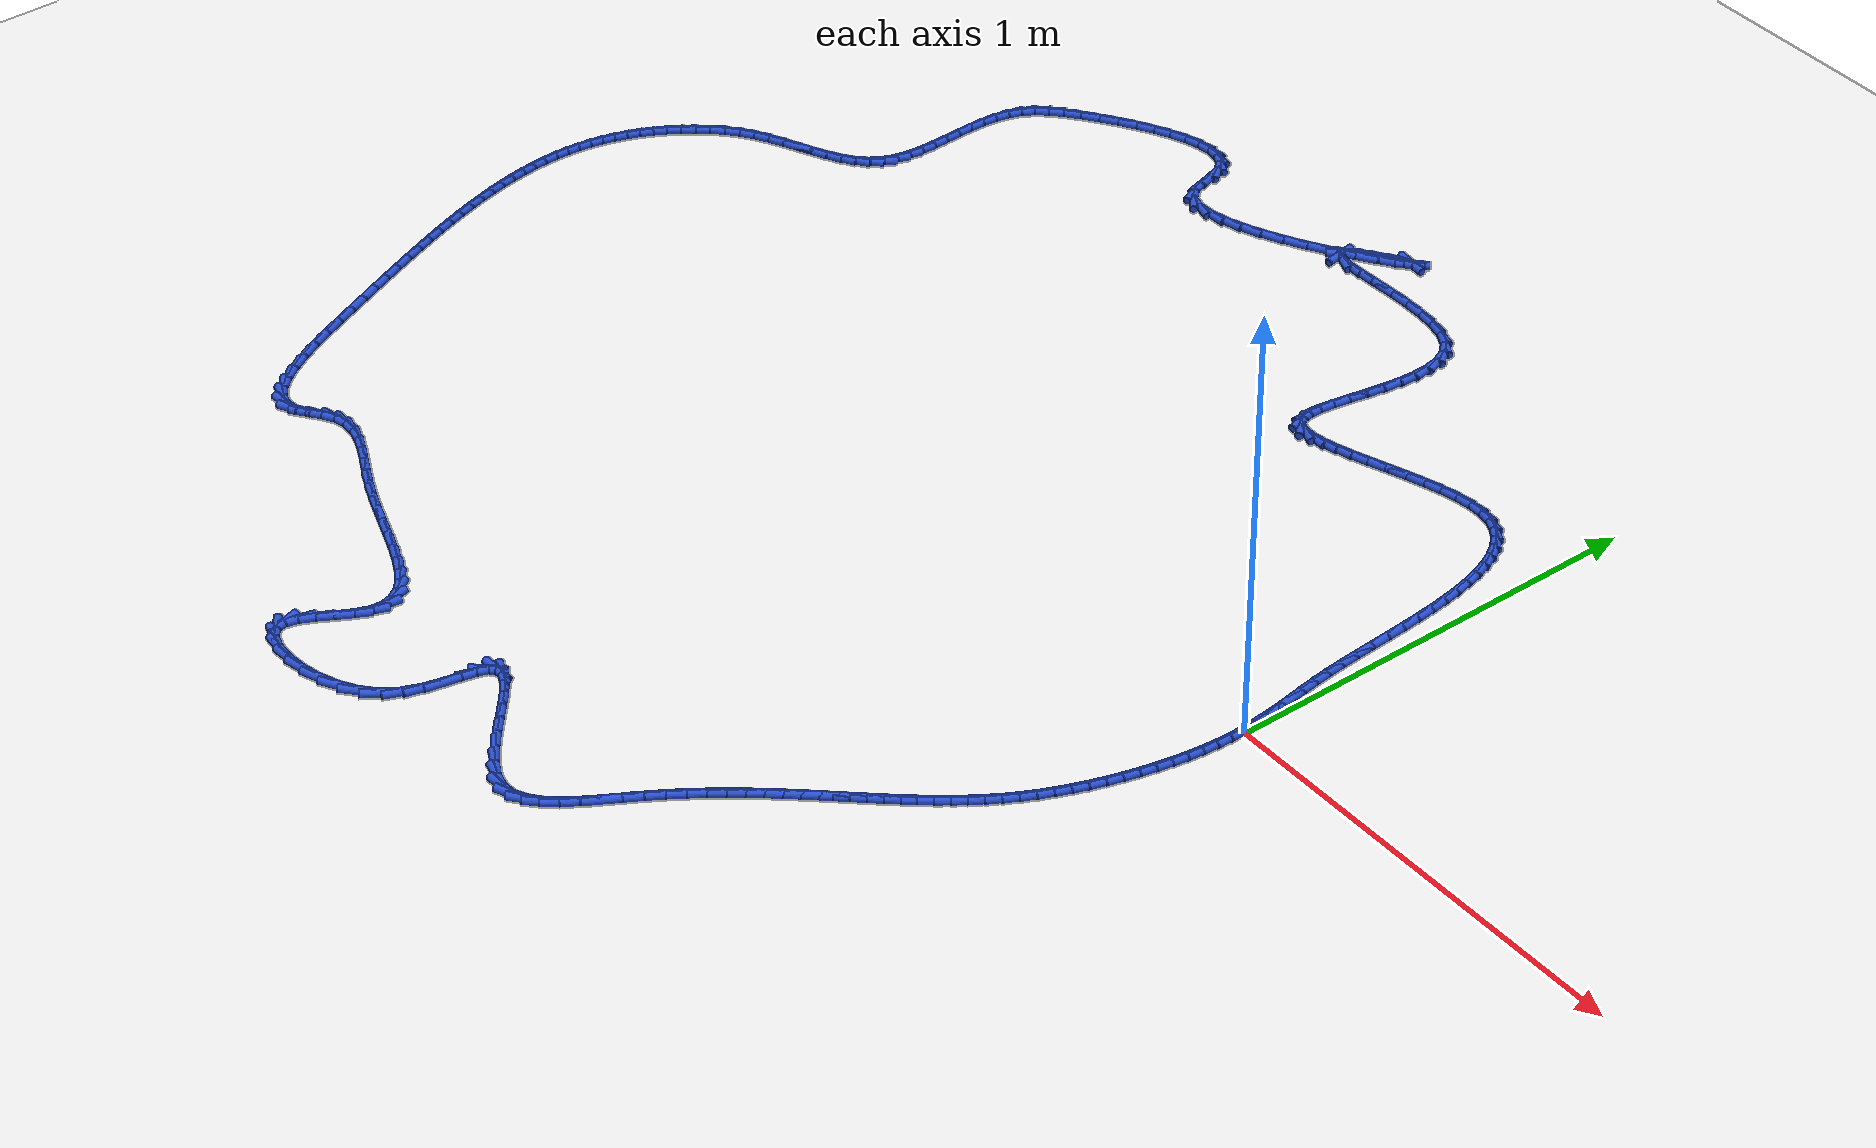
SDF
<sdf version="1.6">
 <world name="default">
  <light name="sun" type="directional">
   <pose>0 0 10 0 -0 0</pose>
   <diffuse>0.8 0.8 0.8 1</diffuse>
   <specular>0.2 0.2 0.2 1</specular>
   <attenuation>
    <range>1000</range>
    <constant>0.9</constant>
    <linear>0.01</linear>
    <quadratic>0.001</quadratic>
   </attenuation>
   <direction>-0.5 0.1 -0.9</direction>
  </light>
  <model name="ground_plane">
   <static>1</static>
   <link name="link">
    <collision name="collision">
     <geometry><plane><normal>0 0 1</normal><size>100 100</size></plane></geometry>
     <surface><friction><ode><mu>100</mu><mu2>50</mu2></ode></friction></surface>
    </collision>
    <visual name="visual">
     <cast_shadows>0</cast_shadows>
     <geometry><plane><normal>0 0 1</normal><size>100 100</size></plane></geometry>
     <material>
      <script><uri>file://media/materials/scripts/gazebo.material</uri><name>Gazebo/WhiteGlow</name></script>
     </material>
    </visual>
   </link>
  </model>
  <gravity>0 0 -9.8</gravity>
  <magnetic_field>6e-06 2.3e-05 -4.2e-05</magnetic_field>
  <atmosphere type="adiabatic"/>
  <physics name="default_physics" default="0" type="ode">
   <max_step_size>0.001</max_step_size>
   <real_time_factor>1</real_time_factor>
   <real_time_update_rate>1000</real_time_update_rate>
  </physics>
  <scene><ambient>0.4 0.4 0.4 1</ambient><background>0.7 0.7 0.7 1</background><shadows>1</shadows></scene>
  <spherical_coordinates>
   <surface_model>EARTH_WGS84</surface_model>
   <latitude_deg>0</latitude_deg>
   <longitude_deg>0</longitude_deg>
   <elevation>0</elevation>
   <heading_deg>0</heading_deg>
  </spherical_coordinates>
  <model name="line">
   <link name="link_0">
    <pose>1.5612511283791264e-17 -1.3877787807814457e-17 0.01 0 1.57 -1.5118390819186485</pose>
    <collision name="collision">
     <geometry><cylinder><radius>0.01</radius><length>0.08</length></cylinder></geometry>
    </collision>
    <visual name="visual">
     <material>
      <script><name>Gazebo/Blue</name><uri>file://media/materials/scripts/gazebo.material</uri></script>
     </material>
     <geometry><cylinder><radius>0.01</radius><length>0.08</length></cylinder></geometry>
    </visual>
   </link>
   <link name="link_1">
    <pose>-0.0019415017721792643 0.032892509299139325 0.01 0 1.57 -1.4699527122502627</pose>
    <collision name="collision">
     <geometry><cylinder><radius>0.01</radius><length>0.08</length></cylinder></geometry>
    </collision>
    <visual name="visual">
     <material>
      <script><name>Gazebo/Blue</name><uri>file://media/materials/scripts/gazebo.material</uri></script>
     </material>
     <geometry><cylinder><radius>0.01</radius><length>0.08</length></cylinder></geometry>
    </visual>
   </link>
   <link name="link_2">
    <pose>-0.005248764462979722 0.06557721720528396 0.01 0 1.57 -1.4408107136291277</pose>
    <collision name="collision">
     <geometry><cylinder><radius>0.01</radius><length>0.08</length></cylinder></geometry>
    </collision>
    <visual name="visual">
     <material>
      <script><name>Gazebo/Blue</name><uri>file://media/materials/scripts/gazebo.material</uri></script>
     </material>
     <geometry><cylinder><radius>0.01</radius><length>0.08</length></cylinder></geometry>
    </visual>
   </link>
   <link name="link_3">
    <pose>-0.009543673569140288 0.09843233410015827 0.01 0 1.57 -1.425014783909602</pose>
    <collision name="collision">
     <geometry><cylinder><radius>0.01</radius><length>0.08</length></cylinder></geometry>
    </collision>
    <visual name="visual">
     <material>
      <script><name>Gazebo/Blue</name><uri>file://media/materials/scripts/gazebo.material</uri></script>
     </material>
     <geometry><cylinder><radius>0.01</radius><length>0.08</length></cylinder></geometry>
    </visual>
   </link>
   <link name="link_4">
    <pose>-0.014448114587399889 0.13183607036548653 0.01 0 1.57 -1.4222974363183094</pose>
    <collision name="collision">
     <geometry><cylinder><radius>0.01</radius><length>0.08</length></cylinder></geometry>
    </collision>
    <visual name="visual">
     <material>
      <script><name>Gazebo/Blue</name><uri>file://media/materials/scripts/gazebo.material</uri></script>
     </material>
     <geometry><cylinder><radius>0.01</radius><length>0.08</length></cylinder></geometry>
    </visual>
   </link>
   <link name="link_5">
    <pose>-0.019583973014497453 0.16616663638299312 0.01 0 1.57 -1.431695528400672</pose>
    <collision name="collision">
     <geometry><cylinder><radius>0.01</radius><length>0.08</length></cylinder></geometry>
    </collision>
    <visual name="visual">
     <material>
      <script><name>Gazebo/Blue</name><uri>file://media/materials/scripts/gazebo.material</uri></script>
     </material>
     <geometry><cylinder><radius>0.01</radius><length>0.08</length></cylinder></geometry>
    </visual>
   </link>
   <link name="link_6">
    <pose>-0.024573134347171902 0.20180224253440227 0.01 0 1.57 -1.4517349405809672</pose>
    <collision name="collision">
     <geometry><cylinder><radius>0.01</radius><length>0.08</length></cylinder></geometry>
    </collision>
    <visual name="visual">
     <material>
      <script><name>Gazebo/Blue</name><uri>file://media/materials/scripts/gazebo.material</uri></script>
     </material>
     <geometry><cylinder><radius>0.01</radius><length>0.08</length></cylinder></geometry>
    </visual>
   </link>
   <link name="link_7">
    <pose>-0.02903748408216217 0.23912109920143837 0.01 0 1.57 -1.4776081850824199</pose>
    <collision name="collision">
     <geometry><cylinder><radius>0.01</radius><length>0.08</length></cylinder></geometry>
    </collision>
    <visual name="visual">
     <material>
      <script><name>Gazebo/Blue</name><uri>file://media/materials/scripts/gazebo.material</uri></script>
     </material>
     <geometry><cylinder><radius>0.01</radius><length>0.08</length></cylinder></geometry>
    </visual>
   </link>
   <link name="link_8">
    <pose>-0.032705312508177965 0.27836649062140445 0.01 0 1.57 -1.4967464867715143</pose>
    <collision name="collision">
     <geometry><cylinder><radius>0.01</radius><length>0.08</length></cylinder></geometry>
    </collision>
    <visual name="visual">
     <material>
      <script><name>Gazebo/Blue</name><uri>file://media/materials/scripts/gazebo.material</uri></script>
     </material>
     <geometry><cylinder><radius>0.01</radius><length>0.08</length></cylinder></geometry>
    </visual>
   </link>
   <link name="link_9">
    <pose>-0.03573706674442917 0.3192337063986119 0.01 0 1.57 -1.5074773160996524</pose>
    <collision name="collision">
     <geometry><cylinder><radius>0.01</radius><length>0.08</length></cylinder></geometry>
    </collision>
    <visual name="visual">
     <material>
      <script><name>Gazebo/Blue</name><uri>file://media/materials/scripts/gazebo.material</uri></script>
     </material>
     <geometry><cylinder><radius>0.01</radius><length>0.08</length></cylinder></geometry>
    </visual>
   </link>
   <link name="link_10">
    <pose>-0.03840289256038804 0.361278933229937 0.01 0 1.57 -1.5107918281252322</pose>
    <collision name="collision">
     <geometry><cylinder><radius>0.01</radius><length>0.08</length></cylinder></geometry>
    </collision>
    <visual name="visual">
     <material>
      <script><name>Gazebo/Blue</name><uri>file://media/materials/scripts/gazebo.material</uri></script>
     </material>
     <geometry><cylinder><radius>0.01</radius><length>0.08</length></cylinder></geometry>
    </visual>
   </link>
   <link name="link_11">
    <pose>-0.04097293573970034 0.4040583577942836 0.01 0 1.57 -1.5071624007485722</pose>
    <collision name="collision">
     <geometry><cylinder><radius>0.01</radius><length>0.08</length></cylinder></geometry>
    </collision>
    <visual name="visual">
     <material>
      <script><name>Gazebo/Blue</name><uri>file://media/materials/scripts/gazebo.material</uri></script>
     </material>
     <geometry><cylinder><radius>0.01</radius><length>0.08</length></cylinder></geometry>
    </visual>
   </link>
   <link name="link_12">
    <pose>-0.04371734206601181 0.44712816677055567 0.01 0 1.57 -1.4966273112997701</pose>
    <collision name="collision">
     <geometry><cylinder><radius>0.01</radius><length>0.08</length></cylinder></geometry>
    </collision>
    <visual name="visual">
     <material>
      <script><name>Gazebo/Blue</name><uri>file://media/materials/scripts/gazebo.material</uri></script>
     </material>
     <geometry><cylinder><radius>0.01</radius><length>0.08</length></cylinder></geometry>
    </visual>
   </link>
   <link name="link_13">
    <pose>-0.046906257322968194 0.4900445468376572 0.01 0 1.57 -1.4788153640142214</pose>
    <collision name="collision">
     <geometry><cylinder><radius>0.01</radius><length>0.08</length></cylinder></geometry>
    </collision>
    <visual name="visual">
     <material>
      <script><name>Gazebo/Blue</name><uri>file://media/materials/scripts/gazebo.material</uri></script>
     </material>
     <geometry><cylinder><radius>0.01</radius><length>0.08</length></cylinder></geometry>
    </visual>
   </link>
   <link name="link_14">
    <pose>-0.050809827294215244 0.532363684674492 0.01 0 1.57 -1.4529200065143062</pose>
    <collision name="collision">
     <geometry><cylinder><radius>0.01</radius><length>0.08</length></cylinder></geometry>
    </collision>
    <visual name="visual">
     <material>
      <script><name>Gazebo/Blue</name><uri>file://media/materials/scripts/gazebo.material</uri></script>
     </material>
     <geometry><cylinder><radius>0.01</radius><length>0.08</length></cylinder></geometry>
    </visual>
   </link>
   <link name="link_15">
    <pose>-0.055698197763398696 0.5736417669599638 0.01 0 1.57 -1.4176245442067188</pose>
    <collision name="collision">
     <geometry><cylinder><radius>0.01</radius><length>0.08</length></cylinder></geometry>
    </collision>
    <visual name="visual">
     <material>
      <script><name>Gazebo/Blue</name><uri>file://media/materials/scripts/gazebo.material</uri></script>
     </material>
     <geometry><cylinder><radius>0.01</radius><length>0.08</length></cylinder></geometry>
    </visual>
   </link>
   <link name="link_16">
    <pose>-0.061841514514164295 0.6134349803729767 0.01 0 1.57 -1.3709767385991372</pose>
    <collision name="collision">
     <geometry><cylinder><radius>0.01</radius><length>0.08</length></cylinder></geometry>
    </collision>
    <visual name="visual">
     <material>
      <script><name>Gazebo/Blue</name><uri>file://media/materials/scripts/gazebo.material</uri></script>
     </material>
     <geometry><cylinder><radius>0.01</radius><length>0.08</length></cylinder></geometry>
    </visual>
   </link>
   <link name="link_17">
    <pose>-0.06950992333015779 0.6512995115924345 0.01 0 1.57 -1.310217509264038</pose>
    <collision name="collision">
     <geometry><cylinder><radius>0.01</radius><length>0.08</length></cylinder></geometry>
    </collision>
    <visual name="visual">
     <material>
      <script><name>Gazebo/Blue</name><uri>file://media/materials/scripts/gazebo.material</uri></script>
     </material>
     <geometry><cylinder><radius>0.01</radius><length>0.08</length></cylinder></geometry>
    </visual>
   </link>
   <link name="link_18">
    <pose>-0.07897356999502493 0.6867915472972412 0.01 0 1.57 -1.231601118944008</pose>
    <collision name="collision">
     <geometry><cylinder><radius>0.01</radius><length>0.08</length></cylinder></geometry>
    </collision>
    <visual name="visual">
     <material>
      <script><name>Gazebo/Blue</name><uri>file://media/materials/scripts/gazebo.material</uri></script>
     </material>
     <geometry><cylinder><radius>0.01</radius><length>0.08</length></cylinder></geometry>
    </visual>
   </link>
   <link name="link_19">
    <pose>-0.09050260029241144 0.7194672741663006 0.01 0 1.57 -1.1303437791452464</pose>
    <collision name="collision">
     <geometry><cylinder><radius>0.01</radius><length>0.08</length></cylinder></geometry>
    </collision>
    <visual name="visual">
     <material>
      <script><name>Gazebo/Blue</name><uri>file://media/materials/scripts/gazebo.material</uri></script>
     </material>
     <geometry><cylinder><radius>0.01</radius><length>0.08</length></cylinder></geometry>
    </visual>
   </link>
   <link name="link_20">
    <pose>-0.1043671600059631 0.7488828788785167 0.01 0 1.57 -1.0010758105745496</pose>
    <collision name="collision">
     <geometry><cylinder><radius>0.01</radius><length>0.08</length></cylinder></geometry>
    </collision>
    <visual name="visual">
     <material>
      <script><name>Gazebo/Blue</name><uri>file://media/materials/scripts/gazebo.material</uri></script>
     </material>
     <geometry><cylinder><radius>0.01</radius><length>0.08</length></cylinder></geometry>
    </visual>
   </link>
   <link name="link_21">
    <pose>-0.12083739491932563 0.7745945481127933 0.01 0 1.57 -0.8395584375596473</pose>
    <collision name="collision">
     <geometry><cylinder><radius>0.01</radius><length>0.08</length></cylinder></geometry>
    </collision>
    <visual name="visual">
     <material>
      <script><name>Gazebo/Blue</name><uri>file://media/materials/scripts/gazebo.material</uri></script>
     </material>
     <geometry><cylinder><radius>0.01</radius><length>0.08</length></cylinder></geometry>
    </visual>
   </link>
   <link name="link_22">
    <pose>-0.14018345081614478 0.7961584685480343 0.01 0 1.57 -0.646435158526174</pose>
    <collision name="collision">
     <geometry><cylinder><radius>0.01</radius><length>0.08</length></cylinder></geometry>
    </collision>
    <visual name="visual">
     <material>
      <script><name>Gazebo/Blue</name><uri>file://media/materials/scripts/gazebo.material</uri></script>
     </material>
     <geometry><cylinder><radius>0.01</radius><length>0.08</length></cylinder></geometry>
    </visual>
   </link>
   <link name="link_23">
    <pose>-0.16267547348006628 0.8131308268631435 0.01 0 1.57 -0.43175151763653646</pose>
    <collision name="collision">
     <geometry><cylinder><radius>0.01</radius><length>0.08</length></cylinder></geometry>
    </collision>
    <visual name="visual">
     <material>
      <script><name>Gazebo/Blue</name><uri>file://media/materials/scripts/gazebo.material</uri></script>
     </material>
     <geometry><cylinder><radius>0.01</radius><length>0.08</length></cylinder></geometry>
    </visual>
   </link>
   <link name="link_24">
    <pose>-0.18858360869473587 0.8250678097370249 0.01 0 1.57 -0.21484234970169563</pose>
    <collision name="collision">
     <geometry><cylinder><radius>0.01</radius><length>0.08</length></cylinder></geometry>
    </collision>
    <visual name="visual">
     <material>
      <script><name>Gazebo/Blue</name><uri>file://media/materials/scripts/gazebo.material</uri></script>
     </material>
     <geometry><cylinder><radius>0.01</radius><length>0.08</length></cylinder></geometry>
    </visual>
   </link>
   <link name="link_25">
    <pose>-0.2181780022437993 0.8315256038485823 0.01 0 1.57 -0.021126260409827718</pose>
    <collision name="collision">
     <geometry><cylinder><radius>0.01</radius><length>0.08</length></cylinder></geometry>
    </collision>
    <visual name="visual">
     <material>
      <script><name>Gazebo/Blue</name><uri>file://media/materials/scripts/gazebo.material</uri></script>
     </material>
     <geometry><cylinder><radius>0.01</radius><length>0.08</length></cylinder></geometry>
    </visual>
   </link>
   <link name="link_26">
    <pose>-0.25160198475441264 0.8322318326779146 0.01 0 1.57 0.11825566839608</pose>
    <collision name="collision">
     <geometry><cylinder><radius>0.01</radius><length>0.08</length></cylinder></geometry>
    </collision>
    <visual name="visual">
     <material>
      <script><name>Gazebo/Blue</name><uri>file://media/materials/scripts/gazebo.material</uri></script>
     </material>
     <geometry><cylinder><radius>0.01</radius><length>0.08</length></cylinder></geometry>
    </visual>
   </link>
   <link name="link_27">
    <pose>-0.2882896018206109 0.8278729763637357 0.01 0 1.57 0.2115178158600336</pose>
    <collision name="collision">
     <geometry><cylinder><radius>0.01</radius><length>0.08</length></cylinder></geometry>
    </collision>
    <visual name="visual">
     <material>
      <script><name>Gazebo/Blue</name><uri>file://media/materials/scripts/gazebo.material</uri></script>
     </material>
     <geometry><cylinder><radius>0.01</radius><length>0.08</length></cylinder></geometry>
    </visual>
   </link>
   <link name="link_28">
    <pose>-0.32742843103578745 0.8194687061774 0.01 0 1.57 0.27328191515543776</pose>
    <collision name="collision">
     <geometry><cylinder><radius>0.01</radius><length>0.08</length></cylinder></geometry>
    </collision>
    <visual name="visual">
     <material>
      <script><name>Gazebo/Blue</name><uri>file://media/materials/scripts/gazebo.material</uri></script>
     </material>
     <geometry><cylinder><radius>0.01</radius><length>0.08</length></cylinder></geometry>
    </visual>
   </link>
   <link name="link_29">
    <pose>-0.368205803464725 0.8080390266633322 0.01 0 1.57 0.3123617350956508</pose>
    <collision name="collision">
     <geometry><cylinder><radius>0.01</radius><length>0.08</length></cylinder></geometry>
    </collision>
    <visual name="visual">
     <material>
      <script><name>Gazebo/Blue</name><uri>file://media/materials/scripts/gazebo.material</uri></script>
     </material>
     <geometry><cylinder><radius>0.01</radius><length>0.08</length></cylinder></geometry>
    </visual>
   </link>
   <link name="link_30">
    <pose>-0.4098090501722063 0.794603942365956 0.01 0 1.57 0.3335616188444252</pose>
    <collision name="collision">
     <geometry><cylinder><radius>0.01</radius><length>0.08</length></cylinder></geometry>
    </collision>
    <visual name="visual">
     <material>
      <script><name>Gazebo/Blue</name><uri>file://media/materials/scripts/gazebo.material</uri></script>
     </material>
     <geometry><cylinder><radius>0.01</radius><length>0.08</length></cylinder></geometry>
    </visual>
   </link>
   <link name="link_31">
    <pose>-0.45142550222301414 0.780183457829696 0.01 0 1.57 0.33885431014899253</pose>
    <collision name="collision">
     <geometry><cylinder><radius>0.01</radius><length>0.08</length></cylinder></geometry>
    </collision>
    <visual name="visual">
     <material>
      <script><name>Gazebo/Blue</name><uri>file://media/materials/scripts/gazebo.material</uri></script>
     </material>
     <geometry><cylinder><radius>0.01</radius><length>0.08</length></cylinder></geometry>
    </visual>
   </link>
   <link name="link_32">
    <pose>-0.49224249068193077 0.7657975775989757 0.01 0 1.57 0.32777555426560195</pose>
    <collision name="collision">
     <geometry><cylinder><radius>0.01</radius><length>0.08</length></cylinder></geometry>
    </collision>
    <visual name="visual">
     <material>
      <script><name>Gazebo/Blue</name><uri>file://media/materials/scripts/gazebo.material</uri></script>
     </material>
     <geometry><cylinder><radius>0.01</radius><length>0.08</length></cylinder></geometry>
    </visual>
   </link>
   <link name="link_33">
    <pose>-0.5314473466137393 0.75246630621822 0.01 0 1.57 0.29700101034942195</pose>
    <collision name="collision">
     <geometry><cylinder><radius>0.01</radius><length>0.08</length></cylinder></geometry>
    </collision>
    <visual name="visual">
     <material>
      <script><name>Gazebo/Blue</name><uri>file://media/materials/scripts/gazebo.material</uri></script>
     </material>
     <geometry><cylinder><radius>0.01</radius><length>0.08</length></cylinder></geometry>
    </visual>
   </link>
   <link name="link_34">
    <pose>-0.5682274010832223 0.7412096482318526 0.01 0 1.57 0.23869469505411492</pose>
    <collision name="collision">
     <geometry><cylinder><radius>0.01</radius><length>0.08</length></cylinder></geometry>
    </collision>
    <visual name="visual">
     <material>
      <script><name>Gazebo/Blue</name><uri>file://media/materials/scripts/gazebo.material</uri></script>
     </material>
     <geometry><cylinder><radius>0.01</radius><length>0.08</length></cylinder></geometry>
    </visual>
   </link>
   <link name="link_35">
    <pose>-0.6017699851551626 0.7330476081842976 0.01 0 1.57 0.1363837995734624</pose>
    <collision name="collision">
     <geometry><cylinder><radius>0.01</radius><length>0.08</length></cylinder></geometry>
    </collision>
    <visual name="visual">
     <material>
      <script><name>Gazebo/Blue</name><uri>file://media/materials/scripts/gazebo.material</uri></script>
     </material>
     <geometry><cylinder><radius>0.01</radius><length>0.08</length></cylinder></geometry>
    </visual>
   </link>
   <link name="link_36">
    <pose>-0.6312624298943424 0.7290001906199794 0.01 0 1.57 -0.04411368922124703</pose>
    <collision name="collision">
     <geometry><cylinder><radius>0.01</radius><length>0.08</length></cylinder></geometry>
    </collision>
    <visual name="visual">
     <material>
      <script><name>Gazebo/Blue</name><uri>file://media/materials/scripts/gazebo.material</uri></script>
     </material>
     <geometry><cylinder><radius>0.01</radius><length>0.08</length></cylinder></geometry>
    </visual>
   </link>
   <link name="link_37">
    <pose>-0.6558920663655448 0.7300874000833221 0.01 0 1.57 -0.36495574321376256</pose>
    <collision name="collision">
     <geometry><cylinder><radius>0.01</radius><length>0.08</length></cylinder></geometry>
    </collision>
    <visual name="visual">
     <material>
      <script><name>Gazebo/Blue</name><uri>file://media/materials/scripts/gazebo.material</uri></script>
     </material>
     <geometry><cylinder><radius>0.01</radius><length>0.08</length></cylinder></geometry>
    </visual>
   </link>
   <link name="link_38">
    <pose>-0.6748462256335522 0.7373292411187496 0.01 0 1.57 -0.8576139744715884</pose>
    <collision name="collision">
     <geometry><cylinder><radius>0.01</radius><length>0.08</length></cylinder></geometry>
    </collision>
    <visual name="visual">
     <material>
      <script><name>Gazebo/Blue</name><uri>file://media/materials/scripts/gazebo.material</uri></script>
     </material>
     <geometry><cylinder><radius>0.01</radius><length>0.08</length></cylinder></geometry>
    </visual>
   </link>
   <link name="link_39">
    <pose>-0.6873150746168148 0.7517428073425478 0.01 0 1.57 -1.3129137072464439</pose>
    <collision name="collision">
     <geometry><cylinder><radius>0.01</radius><length>0.08</length></cylinder></geometry>
    </collision>
    <visual name="visual">
     <material>
      <script><name>Gazebo/Blue</name><uri>file://media/materials/scripts/gazebo.material</uri></script>
     </material>
     <geometry><cylinder><radius>0.01</radius><length>0.08</length></cylinder></geometry>
    </visual>
   </link>
   <link name="link_40">
    <pose>-0.6931087347726045 0.7737088255752533 0.01 0 1.57 -1.5595175447682645</pose>
    <collision name="collision">
     <geometry><cylinder><radius>0.01</radius><length>0.08</length></cylinder></geometry>
    </collision>
    <visual name="visual">
     <material>
      <script><name>Gazebo/Blue</name><uri>file://media/materials/scripts/gazebo.material</uri></script>
     </material>
     <geometry><cylinder><radius>0.01</radius><length>0.08</length></cylinder></geometry>
    </visual>
   </link>
   <link name="link_41">
    <pose>-0.6934298531334976 0.8021786322823617 0.01 0 1.57 1.4598133642609663</pose>
    <collision name="collision">
     <geometry><cylinder><radius>0.01</radius><length>0.08</length></cylinder></geometry>
    </collision>
    <visual name="visual">
     <material>
      <script><name>Gazebo/Blue</name><uri>file://media/materials/scripts/gazebo.material</uri></script>
     </material>
     <geometry><cylinder><radius>0.01</radius><length>0.08</length></cylinder></geometry>
    </visual>
   </link>
   <link name="link_42">
    <pose>-0.6896709483146134 0.8359086658150382 0.01 0 1.57 1.4016474509683845</pose>
    <collision name="collision">
     <geometry><cylinder><radius>0.01</radius><length>0.08</length></cylinder></geometry>
    </collision>
    <visual name="visual">
     <material>
      <script><name>Gazebo/Blue</name><uri>file://media/materials/scripts/gazebo.material</uri></script>
     </material>
     <geometry><cylinder><radius>0.01</radius><length>0.08</length></cylinder></geometry>
    </visual>
   </link>
   <link name="link_43">
    <pose>-0.6832245389310723 0.8736553645244467 0.01 0 1.57 1.382019085787752</pose>
    <collision name="collision">
     <geometry><cylinder><radius>0.01</radius><length>0.08</length></cylinder></geometry>
    </collision>
    <visual name="visual">
     <material>
      <script><name>Gazebo/Blue</name><uri>file://media/materials/scripts/gazebo.material</uri></script>
     </material>
     <geometry><cylinder><radius>0.01</radius><length>0.08</length></cylinder></geometry>
    </visual>
   </link>
   <link name="link_44">
    <pose>-0.6754831435979937 0.914175166761752 0.01 0 1.57 1.3909767279148109</pose>
    <collision name="collision">
     <geometry><cylinder><radius>0.01</radius><length>0.08</length></cylinder></geometry>
    </collision>
    <visual name="visual">
     <material>
      <script><name>Gazebo/Blue</name><uri>file://media/materials/scripts/gazebo.material</uri></script>
     </material>
     <geometry><cylinder><radius>0.01</radius><length>0.08</length></cylinder></geometry>
    </visual>
   </link>
   <link name="link_45">
    <pose>-0.6678392809304983 0.9562245108781192 0.01 0 1.57 1.4264485243379388</pose>
    <collision name="collision">
     <geometry><cylinder><radius>0.01</radius><length>0.08</length></cylinder></geometry>
    </collision>
    <visual name="visual">
     <material>
      <script><name>Gazebo/Blue</name><uri>file://media/materials/scripts/gazebo.material</uri></script>
     </material>
     <geometry><cylinder><radius>0.01</radius><length>0.08</length></cylinder></geometry>
    </visual>
   </link>
   <link name="link_46">
    <pose>-0.6616854695437054 0.9985598352247133 0.01 0 1.57 1.4919024230707973</pose>
    <collision name="collision">
     <geometry><cylinder><radius>0.01</radius><length>0.08</length></cylinder></geometry>
    </collision>
    <visual name="visual">
     <material>
      <script><name>Gazebo/Blue</name><uri>file://media/materials/scripts/gazebo.material</uri></script>
     </material>
     <geometry><cylinder><radius>0.01</radius><length>0.08</length></cylinder></geometry>
    </visual>
   </link>
   <link name="link_47">
    <pose>-0.6584142280527352 1.0399375781526985 0.01 0 1.57 -1.545178294317305</pose>
    <collision name="collision">
     <geometry><cylinder><radius>0.01</radius><length>0.08</length></cylinder></geometry>
    </collision>
    <visual name="visual">
     <material>
      <script><name>Gazebo/Blue</name><uri>file://media/materials/scripts/gazebo.material</uri></script>
     </material>
     <geometry><cylinder><radius>0.01</radius><length>0.08</length></cylinder></geometry>
    </visual>
   </link>
   <link name="link_48">
    <pose>-0.6594180750727076 1.0791141780132392 0.01 0 1.57 -1.386212953670389</pose>
    <collision name="collision">
     <geometry><cylinder><radius>0.01</radius><length>0.08</length></cylinder></geometry>
    </collision>
    <visual name="visual">
     <material>
      <script><name>Gazebo/Blue</name><uri>file://media/materials/scripts/gazebo.material</uri></script>
     </material>
     <geometry><cylinder><radius>0.01</radius><length>0.08</length></cylinder></geometry>
    </visual>
   </link>
   <link name="link_49">
    <pose>-0.6660895292187425 1.114846073157501 0.01 0 1.57 -1.1543376628106674</pose>
    <collision name="collision">
     <geometry><cylinder><radius>0.01</radius><length>0.08</length></cylinder></geometry>
    </collision>
    <visual name="visual">
     <material>
      <script><name>Gazebo/Blue</name><uri>file://media/materials/scripts/gazebo.material</uri></script>
     </material>
     <geometry><cylinder><radius>0.01</radius><length>0.08</length></cylinder></geometry>
    </visual>
   </link>
   <link name="link_50">
    <pose>-0.6798211091059598 1.1458897019366479 0.01 0 1.57 -0.8472182868405171</pose>
    <collision name="collision">
     <geometry><cylinder><radius>0.01</radius><length>0.08</length></cylinder></geometry>
    </collision>
    <visual name="visual">
     <material>
      <script><name>Gazebo/Blue</name><uri>file://media/materials/scripts/gazebo.material</uri></script>
     </material>
     <geometry><cylinder><radius>0.01</radius><length>0.08</length></cylinder></geometry>
    </visual>
   </link>
   <link name="link_51">
    <pose>-0.7020053333494796 1.171001502701845 0.01 0 1.57 -0.5179572351718453</pose>
    <collision name="collision">
     <geometry><cylinder><radius>0.01</radius><length>0.08</length></cylinder></geometry>
    </collision>
    <visual name="visual">
     <material>
      <script><name>Gazebo/Blue</name><uri>file://media/materials/scripts/gazebo.material</uri></script>
     </material>
     <geometry><cylinder><radius>0.01</radius><length>0.08</length></cylinder></geometry>
    </visual>
   </link>
   <link name="link_52">
    <pose>-0.7337765556577021 1.1891064149693769 0.01 0 1.57 -0.2807587287827074</pose>
    <collision name="collision">
     <geometry><cylinder><radius>0.01</radius><length>0.08</length></cylinder></geometry>
    </collision>
    <visual name="visual">
     <material>
      <script><name>Gazebo/Blue</name><uri>file://media/materials/scripts/gazebo.material</uri></script>
     </material>
     <geometry><cylinder><radius>0.01</radius><length>0.08</length></cylinder></geometry>
    </visual>
   </link>
   <link name="link_53">
    <pose>-0.7738985429935397 1.2006766320388107 0.01 0 1.57 -0.13707496246987613</pose>
    <collision name="collision">
     <geometry><cylinder><radius>0.01</radius><length>0.08</length></cylinder></geometry>
    </collision>
    <visual name="visual">
     <material>
      <script><name>Gazebo/Blue</name><uri>file://media/materials/scripts/gazebo.material</uri></script>
     </material>
     <geometry><cylinder><radius>0.01</radius><length>0.08</length></cylinder></geometry>
    </visual>
   </link>
   <link name="link_54">
    <pose>-0.8198600129949541 1.2070165567441948 0.01 0 1.57 -0.04911176284785143</pose>
    <collision name="collision">
     <geometry><cylinder><radius>0.01</radius><length>0.08</length></cylinder></geometry>
    </collision>
    <visual name="visual">
     <material>
      <script><name>Gazebo/Blue</name><uri>file://media/materials/scripts/gazebo.material</uri></script>
     </material>
     <geometry><cylinder><radius>0.01</radius><length>0.08</length></cylinder></geometry>
    </visual>
   </link>
   <link name="link_55">
    <pose>-0.8691374076711852 1.2094386040764866 0.01 0 1.57 0.0036631736291556022</pose>
    <collision name="collision">
     <geometry><cylinder><radius>0.01</radius><length>0.08</length></cylinder></geometry>
    </collision>
    <visual name="visual">
     <material>
      <script><name>Gazebo/Blue</name><uri>file://media/materials/scripts/gazebo.material</uri></script>
     </material>
     <geometry><cylinder><radius>0.01</radius><length>0.08</length></cylinder></geometry>
    </visual>
   </link>
   <link name="link_56">
    <pose>-0.9192071690314727 1.209255189026647 0.01 0 1.57 0.030534696045813107</pose>
    <collision name="collision">
     <geometry><cylinder><radius>0.01</radius><length>0.08</length></cylinder></geometry>
    </collision>
    <visual name="visual">
     <material>
      <script><name>Gazebo/Blue</name><uri>file://media/materials/scripts/gazebo.material</uri></script>
     </material>
     <geometry><cylinder><radius>0.01</radius><length>0.08</length></cylinder></geometry>
    </visual>
   </link>
   <link name="link_57">
    <pose>-0.9675457390850576 1.207778726585635 0.01 0 1.57 0.0330407969096871</pose>
    <collision name="collision">
     <geometry><cylinder><radius>0.01</radius><length>0.08</length></cylinder></geometry>
    </collision>
    <visual name="visual">
     <material>
      <script><name>Gazebo/Blue</name><uri>file://media/materials/scripts/gazebo.material</uri></script>
     </material>
     <geometry><cylinder><radius>0.01</radius><length>0.08</length></cylinder></geometry>
    </visual>
   </link>
   <link name="link_58">
    <pose>-1.0116295598411802 1.2063216317444097 0.01 0 1.57 0.0033590686071673743</pose>
    <collision name="collision">
     <geometry><cylinder><radius>0.01</radius><length>0.08</length></cylinder></geometry>
    </collision>
    <visual name="visual">
     <material>
      <script><name>Gazebo/Blue</name><uri>file://media/materials/scripts/gazebo.material</uri></script>
     </material>
     <geometry><cylinder><radius>0.01</radius><length>0.08</length></cylinder></geometry>
    </visual>
   </link>
   <link name="link_59">
    <pose>-1.0489350733090803 1.2061963194939314 0.01 0 1.57 -0.08970705878107915</pose>
    <collision name="collision">
     <geometry><cylinder><radius>0.01</radius><length>0.08</length></cylinder></geometry>
    </collision>
    <visual name="visual">
     <material>
      <script><name>Gazebo/Blue</name><uri>file://media/materials/scripts/gazebo.material</uri></script>
     </material>
     <geometry><cylinder><radius>0.01</radius><length>0.08</length></cylinder></geometry>
    </visual>
   </link>
   <link name="link_60">
    <pose>-1.0769387214979982 1.2087152048251588 0.01 0 1.57 -0.3807305800679966</pose>
    <collision name="collision">
     <geometry><cylinder><radius>0.01</radius><length>0.08</length></cylinder></geometry>
    </collision>
    <visual name="visual">
     <material>
      <script><name>Gazebo/Blue</name><uri>file://media/materials/scripts/gazebo.material</uri></script>
     </material>
     <geometry><cylinder><radius>0.01</radius><length>0.08</length></cylinder></geometry>
    </visual>
   </link>
   <link name="link_61">
    <pose>-1.0931169464171742 1.2151907027290512 0.01 0 1.57 -1.416284894749342</pose>
    <collision name="collision">
     <geometry><cylinder><radius>0.01</radius><length>0.08</length></cylinder></geometry>
    </collision>
    <visual name="visual">
     <material>
      <script><name>Gazebo/Blue</name><uri>file://media/materials/scripts/gazebo.material</uri></script>
     </material>
     <geometry><cylinder><radius>0.01</radius><length>0.08</length></cylinder></geometry>
    </visual>
   </link>
   <link name="link_62">
    <pose>-1.0949461900758488 1.2269352281965686 0.01 0 1.57 0.8888373550265114</pose>
    <collision name="collision">
     <geometry><cylinder><radius>0.01</radius><length>0.08</length></cylinder></geometry>
    </collision>
    <visual name="visual">
     <material>
      <script><name>Gazebo/Blue</name><uri>file://media/materials/scripts/gazebo.material</uri></script>
     </material>
     <geometry><cylinder><radius>0.01</radius><length>0.08</length></cylinder></geometry>
    </visual>
   </link>
   <link name="link_63">
    <pose>-1.0801945958808254 1.2451043076114015 0.01 0 1.57 0.6824101287718363</pose>
    <collision name="collision">
     <geometry><cylinder><radius>0.01</radius><length>0.08</length></cylinder></geometry>
    </collision>
    <visual name="visual">
     <material>
      <script><name>Gazebo/Blue</name><uri>file://media/materials/scripts/gazebo.material</uri></script>
     </material>
     <geometry><cylinder><radius>0.01</radius><length>0.08</length></cylinder></geometry>
    </visual>
   </link>
   <link name="link_64">
    <pose>-1.0521869031999154 1.2678649091646335 0.01 0 1.57 0.606022525111661</pose>
    <collision name="collision">
     <geometry><cylinder><radius>0.01</radius><length>0.08</length></cylinder></geometry>
    </collision>
    <visual name="visual">
     <material>
      <script><name>Gazebo/Blue</name><uri>file://media/materials/scripts/gazebo.material</uri></script>
     </material>
     <geometry><cylinder><radius>0.01</radius><length>0.08</length></cylinder></geometry>
    </visual>
   </link>
   <link name="link_65">
    <pose>-1.0192308254464173 1.2907039595234253 0.01 0 1.57 0.5566867503905906</pose>
    <collision name="collision">
     <geometry><cylinder><radius>0.01</radius><length>0.08</length></cylinder></geometry>
    </collision>
    <visual name="visual">
     <material>
      <script><name>Gazebo/Blue</name><uri>file://media/materials/scripts/gazebo.material</uri></script>
     </material>
     <geometry><cylinder><radius>0.01</radius><length>0.08</length></cylinder></geometry>
    </visual>
   </link>
   <link name="link_66">
    <pose>-0.9898106259172549 1.3090134298093439 0.01 0 1.57 0.486553388710373</pose>
    <collision name="collision">
     <geometry><cylinder><radius>0.01</radius><length>0.08</length></cylinder></geometry>
    </collision>
    <visual name="visual">
     <material>
      <script><name>Gazebo/Blue</name><uri>file://media/materials/scripts/gazebo.material</uri></script>
     </material>
     <geometry><cylinder><radius>0.01</radius><length>0.08</length></cylinder></geometry>
    </visual>
   </link>
   <link name="link_67">
    <pose>-0.9719863083919206 1.3184419424890468 0.01 0 1.57 -0.10547685825392154</pose>
    <collision name="collision">
     <geometry><cylinder><radius>0.01</radius><length>0.08</length></cylinder></geometry>
    </collision>
    <visual name="visual">
     <material>
      <script><name>Gazebo/Blue</name><uri>file://media/materials/scripts/gazebo.material</uri></script>
     </material>
     <geometry><cylinder><radius>0.01</radius><length>0.08</length></cylinder></geometry>
    </visual>
   </link>
   <link name="link_68">
    <pose>-0.9681936813811505 1.3180404179658682 0.01 0 1.57 0.790025412645668</pose>
    <collision name="collision">
     <geometry><cylinder><radius>0.01</radius><length>0.08</length></cylinder></geometry>
    </collision>
    <visual name="visual">
     <material>
      <script><name>Gazebo/Blue</name><uri>file://media/materials/scripts/gazebo.material</uri></script>
     </material>
     <geometry><cylinder><radius>0.01</radius><length>0.08</length></cylinder></geometry>
    </visual>
   </link>
   <link name="link_69">
    <pose>-0.976881798797662 1.3092715220208746 0.01 0 1.57 0.6746087191078368</pose>
    <collision name="collision">
     <geometry><cylinder><radius>0.01</radius><length>0.08</length></cylinder></geometry>
    </collision>
    <visual name="visual">
     <material>
      <script><name>Gazebo/Blue</name><uri>file://media/materials/scripts/gazebo.material</uri></script>
     </material>
     <geometry><cylinder><radius>0.01</radius><length>0.08</length></cylinder></geometry>
    </visual>
   </link>
   <link name="link_70">
    <pose>-0.9964151472446874 1.2936490785419925 0.01 0 1.57 0.6301175254867416</pose>
    <collision name="collision">
     <geometry><cylinder><radius>0.01</radius><length>0.08</length></cylinder></geometry>
    </collision>
    <visual name="visual">
     <material>
      <script><name>Gazebo/Blue</name><uri>file://media/materials/scripts/gazebo.material</uri></script>
     </material>
     <geometry><cylinder><radius>0.01</radius><length>0.08</length></cylinder></geometry>
    </visual>
   </link>
   <link name="link_71">
    <pose>-1.025158213325459 1.2726869114171502 0.01 0 1.57 0.5989129284464957</pose>
    <collision name="collision">
     <geometry><cylinder><radius>0.01</radius><length>0.08</length></cylinder></geometry>
    </collision>
    <visual name="visual">
     <material>
      <script><name>Gazebo/Blue</name><uri>file://media/materials/scripts/gazebo.material</uri></script>
     </material>
     <geometry><cylinder><radius>0.01</radius><length>0.08</length></cylinder></geometry>
    </visual>
   </link>
   <link name="link_72">
    <pose>-1.0614754836432096 1.2478988445342751 0.01 0 1.57 0.5702582841455855</pose>
    <collision name="collision">
     <geometry><cylinder><radius>0.01</radius><length>0.08</length></cylinder></geometry>
    </collision>
    <visual name="visual">
     <material>
      <script><name>Gazebo/Blue</name><uri>file://media/materials/scripts/gazebo.material</uri></script>
     </material>
     <geometry><cylinder><radius>0.01</radius><length>0.08</length></cylinder></geometry>
    </visual>
   </link>
   <link name="link_73">
    <pose>-1.1037314448011721 1.220798701781295 0.01 0 1.57 0.5398335683510394</pose>
    <collision name="collision">
     <geometry><cylinder><radius>0.01</radius><length>0.08</length></cylinder></geometry>
    </collision>
    <visual name="visual">
     <material>
      <script><name>Gazebo/Blue</name><uri>file://media/materials/scripts/gazebo.material</uri></script>
     </material>
     <geometry><cylinder><radius>0.01</radius><length>0.08</length></cylinder></geometry>
    </visual>
   </link>
   <link name="link_74">
    <pose>-1.1502905834025785 1.1929003070461361 0.01 0 1.57 0.5045273138398406</pose>
    <collision name="collision">
     <geometry><cylinder><radius>0.01</radius><length>0.08</length></cylinder></geometry>
    </collision>
    <visual name="visual">
     <material>
      <script><name>Gazebo/Blue</name><uri>file://media/materials/scripts/gazebo.material</uri></script>
     </material>
     <geometry><cylinder><radius>0.01</radius><length>0.08</length></cylinder></geometry>
    </visual>
   </link>
   <link name="link_75">
    <pose>-1.1995173860506625 1.165717484216727 0.01 0 1.57 0.46084140385337785</pose>
    <collision name="collision">
     <geometry><cylinder><radius>0.01</radius><length>0.08</length></cylinder></geometry>
    </collision>
    <visual name="visual">
     <material>
      <script><name>Gazebo/Blue</name><uri>file://media/materials/scripts/gazebo.material</uri></script>
     </material>
     <geometry><cylinder><radius>0.01</radius><length>0.08</length></cylinder></geometry>
    </visual>
   </link>
   <link name="link_76">
    <pose>-1.2497763393486552 1.1407640571809947 0.01 0 1.57 0.40368727232913776</pose>
    <collision name="collision">
     <geometry><cylinder><radius>0.01</radius><length>0.08</length></cylinder></geometry>
    </collision>
    <visual name="visual">
     <material>
      <script><name>Gazebo/Blue</name><uri>file://media/materials/scripts/gazebo.material</uri></script>
     </material>
     <geometry><cylinder><radius>0.01</radius><length>0.08</length></cylinder></geometry>
    </visual>
   </link>
   <link name="link_77">
    <pose>-1.2994319298997898 1.1195538498268673 0.01 0 1.57 0.3245493314800192</pose>
    <collision name="collision">
     <geometry><cylinder><radius>0.01</radius><length>0.08</length></cylinder></geometry>
    </collision>
    <visual name="visual">
     <material>
      <script><name>Gazebo/Blue</name><uri>file://media/materials/scripts/gazebo.material</uri></script>
     </material>
     <geometry><cylinder><radius>0.01</radius><length>0.08</length></cylinder></geometry>
    </visual>
   </link>
   <link name="link_78">
    <pose>-1.3468486443072987 1.1036006860422711 0.01 0 1.57 0.20783687385707833</pose>
    <collision name="collision">
     <geometry><cylinder><radius>0.01</radius><length>0.08</length></cylinder></geometry>
    </collision>
    <visual name="visual">
     <material>
      <script><name>Gazebo/Blue</name><uri>file://media/materials/scripts/gazebo.material</uri></script>
     </material>
     <geometry><cylinder><radius>0.01</radius><length>0.08</length></cylinder></geometry>
    </visual>
   </link>
   <link name="link_79">
    <pose>-1.3903909691744145 1.0944183897151347 0.01 0 1.57 0.02359666657394682</pose>
    <collision name="collision">
     <geometry><cylinder><radius>0.01</radius><length>0.08</length></cylinder></geometry>
    </collision>
    <visual name="visual">
     <material>
      <script><name>Gazebo/Blue</name><uri>file://media/materials/scripts/gazebo.material</uri></script>
     </material>
     <geometry><cylinder><radius>0.01</radius><length>0.08</length></cylinder></geometry>
    </visual>
   </link>
   <link name="link_80">
    <pose>-1.42842339110437 1.093520784733385 0.01 0 1.57 -0.28057459466944606</pose>
    <collision name="collision">
     <geometry><cylinder><radius>0.01</radius><length>0.08</length></cylinder></geometry>
    </collision>
    <visual name="visual">
     <material>
      <script><name>Gazebo/Blue</name><uri>file://media/materials/scripts/gazebo.material</uri></script>
     </material>
     <geometry><cylinder><radius>0.01</radius><length>0.08</length></cylinder></geometry>
    </visual>
   </link>
   <link name="link_81">
    <pose>-1.4593103967003973 1.1024216949849497 0.01 0 1.57 -0.7406284928865341</pose>
    <collision name="collision">
     <geometry><cylinder><radius>0.01</radius><length>0.08</length></cylinder></geometry>
    </collision>
    <visual name="visual">
     <material>
      <script><name>Gazebo/Blue</name><uri>file://media/materials/scripts/gazebo.material</uri></script>
     </material>
     <geometry><cylinder><radius>0.01</radius><length>0.08</length></cylinder></geometry>
    </visual>
   </link>
   <link name="link_82">
    <pose>-1.4814178305827517 1.1226332546521056 0.01 0 1.57 -1.1632535250901628</pose>
    <collision name="collision">
     <geometry><cylinder><radius>0.01</radius><length>0.08</length></cylinder></geometry>
    </collision>
    <visual name="visual">
     <material>
      <script><name>Gazebo/Blue</name><uri>file://media/materials/scripts/gazebo.material</uri></script>
     </material>
     <geometry><cylinder><radius>0.01</radius><length>0.08</length></cylinder></geometry>
    </visual>
   </link>
   <link name="link_83">
    <pose>-1.4947819245873377 1.153589227270228 0.01 0 1.57 -1.303703641712374</pose>
    <collision name="collision">
     <geometry><cylinder><radius>0.01</radius><length>0.08</length></cylinder></geometry>
    </collision>
    <visual name="visual">
     <material>
      <script><name>Gazebo/Blue</name><uri>file://media/materials/scripts/gazebo.material</uri></script>
     </material>
     <geometry><cylinder><radius>0.01</radius><length>0.08</length></cylinder></geometry>
    </visual>
   </link>
   <link name="link_84">
    <pose>-1.504361519511522 1.1885984456545444 0.01 0 1.57 -1.2138714838573892</pose>
    <collision name="collision">
     <geometry><cylinder><radius>0.01</radius><length>0.08</length></cylinder></geometry>
    </collision>
    <visual name="visual">
     <material>
      <script><name>Gazebo/Blue</name><uri>file://media/materials/scripts/gazebo.material</uri></script>
     </material>
     <geometry><cylinder><radius>0.01</radius><length>0.08</length></cylinder></geometry>
    </visual>
   </link>
   <link name="link_85">
    <pose>-1.516015226025251 1.219850335533765 0.01 0 1.57 -0.8821710266795205</pose>
    <collision name="collision">
     <geometry><cylinder><radius>0.01</radius><length>0.08</length></cylinder></geometry>
    </collision>
    <visual name="visual">
     <material>
      <script><name>Gazebo/Blue</name><uri>file://media/materials/scripts/gazebo.material</uri></script>
     </material>
     <geometry><cylinder><radius>0.01</radius><length>0.08</length></cylinder></geometry>
    </visual>
   </link>
   <link name="link_86">
    <pose>-1.533961949089617 1.2416560719933765 0.01 0 1.57 -0.47800322293737973</pose>
    <collision name="collision">
     <geometry><cylinder><radius>0.01</radius><length>0.08</length></cylinder></geometry>
    </collision>
    <visual name="visual">
     <material>
      <script><name>Gazebo/Blue</name><uri>file://media/materials/scripts/gazebo.material</uri></script>
     </material>
     <geometry><cylinder><radius>0.01</radius><length>0.08</length></cylinder></geometry>
    </visual>
   </link>
   <link name="link_87">
    <pose>-1.557965453975778 1.2540916998271319 0.01 0 1.57 -0.14047543385359443</pose>
    <collision name="collision">
     <geometry><cylinder><radius>0.01</radius><length>0.08</length></cylinder></geometry>
    </collision>
    <visual name="visual">
     <material>
      <script><name>Gazebo/Blue</name><uri>file://media/materials/scripts/gazebo.material</uri></script>
     </material>
     <geometry><cylinder><radius>0.01</radius><length>0.08</length></cylinder></geometry>
    </visual>
   </link>
   <link name="link_88">
    <pose>-1.587040050487807 1.2582030455686672 0.01 0 1.57 0.09522111268749786</pose>
    <collision name="collision">
     <geometry><cylinder><radius>0.01</radius><length>0.08</length></cylinder></geometry>
    </collision>
    <visual name="visual">
     <material>
      <script><name>Gazebo/Blue</name><uri>file://media/materials/scripts/gazebo.material</uri></script>
     </material>
     <geometry><cylinder><radius>0.01</radius><length>0.08</length></cylinder></geometry>
    </visual>
   </link>
   <link name="link_89">
    <pose>-1.6202000484297752 1.255035935751617 0.01 0 1.57 0.2536501535173192</pose>
    <collision name="collision">
     <geometry><cylinder><radius>0.01</radius><length>0.08</length></cylinder></geometry>
    </collision>
    <visual name="visual">
     <material>
      <script><name>Gazebo/Blue</name><uri>file://media/materials/scripts/gazebo.material</uri></script>
     </material>
     <geometry><cylinder><radius>0.01</radius><length>0.08</length></cylinder></geometry>
    </visual>
   </link>
   <link name="link_90">
    <pose>-1.6564597576057551 1.2456361969096164 0.01 0 1.57 0.36325001997691975</pose>
    <collision name="collision">
     <geometry><cylinder><radius>0.01</radius><length>0.08</length></cylinder></geometry>
    </collision>
    <visual name="visual">
     <material>
      <script><name>Gazebo/Blue</name><uri>file://media/materials/scripts/gazebo.material</uri></script>
     </material>
     <geometry><cylinder><radius>0.01</radius><length>0.08</length></cylinder></geometry>
    </visual>
   </link>
   <link name="link_91">
    <pose>-1.6948334878198184 1.2310496555763002 0.01 0 1.57 0.44270528964713585</pose>
    <collision name="collision">
     <geometry><cylinder><radius>0.01</radius><length>0.08</length></cylinder></geometry>
    </collision>
    <visual name="visual">
     <material>
      <script><name>Gazebo/Blue</name><uri>file://media/materials/scripts/gazebo.material</uri></script>
     </material>
     <geometry><cylinder><radius>0.01</radius><length>0.08</length></cylinder></geometry>
    </visual>
   </link>
   <link name="link_92">
    <pose>-1.734335548876036 1.212322138285303 0.01 0 1.57 0.503193293585269</pose>
    <collision name="collision">
     <geometry><cylinder><radius>0.01</radius><length>0.08</length></cylinder></geometry>
    </collision>
    <visual name="visual">
     <material>
      <script><name>Gazebo/Blue</name><uri>file://media/materials/scripts/gazebo.material</uri></script>
     </material>
     <geometry><cylinder><radius>0.01</radius><length>0.08</length></cylinder></geometry>
    </visual>
   </link>
   <link name="link_93">
    <pose>-1.77398025057848 1.1904994715702606 0.01 0 1.57 0.5515437477851963</pose>
    <collision name="collision">
     <geometry><cylinder><radius>0.01</radius><length>0.08</length></cylinder></geometry>
    </collision>
    <visual name="visual">
     <material>
      <script><name>Gazebo/Blue</name><uri>file://media/materials/scripts/gazebo.material</uri></script>
     </material>
     <geometry><cylinder><radius>0.01</radius><length>0.08</length></cylinder></geometry>
    </visual>
   </link>
   <link name="link_94">
    <pose>-1.8127819027312242 1.1666274819648073 0.01 0 1.57 0.5922388034178889</pose>
    <collision name="collision">
     <geometry><cylinder><radius>0.01</radius><length>0.08</length></cylinder></geometry>
    </collision>
    <visual name="visual">
     <material>
      <script><name>Gazebo/Blue</name><uri>file://media/materials/scripts/gazebo.material</uri></script>
     </material>
     <geometry><cylinder><radius>0.01</radius><length>0.08</length></cylinder></geometry>
    </visual>
   </link>
   <link name="link_95">
    <pose>-1.8497548151383372 1.1417519960025782 0.01 0 1.57 0.6286167172156758</pose>
    <collision name="collision">
     <geometry><cylinder><radius>0.01</radius><length>0.08</length></cylinder></geometry>
    </collision>
    <visual name="visual">
     <material>
      <script><name>Gazebo/Blue</name><uri>file://media/materials/scripts/gazebo.material</uri></script>
     </material>
     <geometry><cylinder><radius>0.01</radius><length>0.08</length></cylinder></geometry>
    </visual>
   </link>
   <link name="link_96">
    <pose>-1.8839132976038928 1.1169188402172083 0.01 0 1.57 0.668778455212116</pose>
    <collision name="collision">
     <geometry><cylinder><radius>0.01</radius><length>0.08</length></cylinder></geometry>
    </collision>
    <visual name="visual">
     <material>
      <script><name>Gazebo/Blue</name><uri>file://media/materials/scripts/gazebo.material</uri></script>
     </material>
     <geometry><cylinder><radius>0.01</radius><length>0.08</length></cylinder></geometry>
    </visual>
   </link>
   <link name="link_97">
    <pose>-1.914344642780417 1.092869927151444 0.01 0 1.57 0.7425305750895814</pose>
    <collision name="collision">
     <geometry><cylinder><radius>0.01</radius><length>0.08</length></cylinder></geometry>
    </collision>
    <visual name="visual">
     <material>
      <script><name>Gazebo/Blue</name><uri>file://media/materials/scripts/gazebo.material</uri></script>
     </material>
     <geometry><cylinder><radius>0.01</radius><length>0.08</length></cylinder></geometry>
    </visual>
   </link>
   <link name="link_98">
    <pose>-1.940489499788269 1.0688757280900114 0.01 0 1.57 0.8649366431658885</pose>
    <collision name="collision">
     <geometry><cylinder><radius>0.01</radius><length>0.08</length></cylinder></geometry>
    </collision>
    <visual name="visual">
     <material>
      <script><name>Gazebo/Blue</name><uri>file://media/materials/scripts/gazebo.material</uri></script>
     </material>
     <geometry><cylinder><radius>0.01</radius><length>0.08</length></cylinder></geometry>
    </visual>
   </link>
   <link name="link_99">
    <pose>-1.961895313201913 1.0437619984240674 0.01 0 1.57 1.036577129346117</pose>
    <collision name="collision">
     <geometry><cylinder><radius>0.01</radius><length>0.08</length></cylinder></geometry>
    </collision>
    <visual name="visual">
     <material>
      <script><name>Gazebo/Blue</name><uri>file://media/materials/scripts/gazebo.material</uri></script>
     </material>
     <geometry><cylinder><radius>0.01</radius><length>0.08</length></cylinder></geometry>
    </visual>
   </link>
   <link name="link_100">
    <pose>-1.9781095874134824 1.0163544445205093 0.01 0 1.57 1.2289908021048956</pose>
    <collision name="collision">
     <geometry><cylinder><radius>0.01</radius><length>0.08</length></cylinder></geometry>
    </collision>
    <visual name="visual">
     <material>
      <script><name>Gazebo/Blue</name><uri>file://media/materials/scripts/gazebo.material</uri></script>
     </material>
     <geometry><cylinder><radius>0.01</radius><length>0.08</length></cylinder></geometry>
    </visual>
   </link>
   <link name="link_101">
    <pose>-1.98896777158298 0.9858341771586407 0.01 0 1.57 1.382902872803384</pose>
    <collision name="collision">
     <geometry><cylinder><radius>0.01</radius><length>0.08</length></cylinder></geometry>
    </collision>
    <visual name="visual">
     <material>
      <script><name>Gazebo/Blue</name><uri>file://media/materials/scripts/gazebo.material</uri></script>
     </material>
     <geometry><cylinder><radius>0.01</radius><length>0.08</length></cylinder></geometry>
    </visual>
   </link>
   <link name="link_102">
    <pose>-1.995287759757469 0.952594919003005 0.01 0 1.57 1.4914013653329543</pose>
    <collision name="collision">
     <geometry><cylinder><radius>0.01</radius><length>0.08</length></cylinder></geometry>
    </collision>
    <visual name="visual">
     <material>
      <script><name>Gazebo/Blue</name><uri>file://media/materials/scripts/gazebo.material</uri></script>
     </material>
     <geometry><cylinder><radius>0.01</radius><length>0.08</length></cylinder></geometry>
    </visual>
   </link>
   <link name="link_103">
    <pose>-1.9980967935933769 0.9172887862449559 0.01 0 1.57 1.561937265028355</pose>
    <collision name="collision">
     <geometry><cylinder><radius>0.01</radius><length>0.08</length></cylinder></geometry>
    </collision>
    <visual name="visual">
     <material>
      <script><name>Gazebo/Blue</name><uri>file://media/materials/scripts/gazebo.material</uri></script>
     </material>
     <geometry><cylinder><radius>0.01</radius><length>0.08</length></cylinder></geometry>
    </visual>
   </link>
   <link name="link_104">
    <pose>-1.998422114747135 0.8805678950758464 0.01 0 1.57 -1.540628234554334</pose>
    <collision name="collision">
     <geometry><cylinder><radius>0.01</radius><length>0.08</length></cylinder></geometry>
    </collision>
    <visual name="visual">
     <material>
      <script><name>Gazebo/Blue</name><uri>file://media/materials/scripts/gazebo.material</uri></script>
     </material>
     <geometry><cylinder><radius>0.01</radius><length>0.08</length></cylinder></geometry>
    </visual>
   </link>
   <link name="link_105">
    <pose>-1.9972909648751709 0.8430843616870302 0.01 0 1.57 -1.5293141313764207</pose>
    <collision name="collision">
     <geometry><cylinder><radius>0.01</radius><length>0.08</length></cylinder></geometry>
    </collision>
    <visual name="visual">
     <material>
      <script><name>Gazebo/Blue</name><uri>file://media/materials/scripts/gazebo.material</uri></script>
     </material>
     <geometry><cylinder><radius>0.01</radius><length>0.08</length></cylinder></geometry>
    </visual>
   </link>
   <link name="link_106">
    <pose>-1.9957305856339138 0.8054903022698598 0.01 0 1.57 -1.5448290793641029</pose>
    <collision name="collision">
     <geometry><cylinder><radius>0.01</radius><length>0.08</length></cylinder></geometry>
    </collision>
    <visual name="visual">
     <material>
      <script><name>Gazebo/Blue</name><uri>file://media/materials/scripts/gazebo.material</uri></script>
     </material>
     <geometry><cylinder><radius>0.01</radius><length>0.08</length></cylinder></geometry>
    </visual>
   </link>
   <link name="link_107">
    <pose>-1.9947682186797933 0.7684378330156888 0.01 0 1.57 1.552312379191864</pose>
    <collision name="collision">
     <geometry><cylinder><radius>0.01</radius><length>0.08</length></cylinder></geometry>
    </collision>
    <visual name="visual">
     <material>
      <script><name>Gazebo/Blue</name><uri>file://media/materials/scripts/gazebo.material</uri></script>
     </material>
     <geometry><cylinder><radius>0.01</radius><length>0.08</length></cylinder></geometry>
    </visual>
   </link>
   <link name="link_108">
    <pose>-1.9954311056692389 0.7325790701158712 0.01 0 1.57 1.4736291321872212</pose>
    <collision name="collision">
     <geometry><cylinder><radius>0.01</radius><length>0.08</length></cylinder></geometry>
    </collision>
    <visual name="visual">
     <material>
      <script><name>Gazebo/Blue</name><uri>file://media/materials/scripts/gazebo.material</uri></script>
     </material>
     <geometry><cylinder><radius>0.01</radius><length>0.08</length></cylinder></geometry>
    </visual>
   </link>
   <link name="link_109">
    <pose>-1.998746488258678 0.6985661297617599 0.01 0 1.57 1.3523757624637018</pose>
    <collision name="collision">
     <geometry><cylinder><radius>0.01</radius><length>0.08</length></cylinder></geometry>
    </collision>
    <visual name="visual">
     <material>
      <script><name>Gazebo/Blue</name><uri>file://media/materials/scripts/gazebo.material</uri></script>
     </material>
     <geometry><cylinder><radius>0.01</radius><length>0.08</length></cylinder></geometry>
    </visual>
   </link>
   <link name="link_110">
    <pose>-2.005741608104542 0.6670511281447079 0.01 0 1.57 1.1795138012131225</pose>
    <collision name="collision">
     <geometry><cylinder><radius>0.01</radius><length>0.08</length></cylinder></geometry>
    </collision>
    <visual name="visual">
     <material>
      <script><name>Gazebo/Blue</name><uri>file://media/materials/scripts/gazebo.material</uri></script>
     </material>
     <geometry><cylinder><radius>0.01</radius><length>0.08</length></cylinder></geometry>
    </visual>
   </link>
   <link name="link_111">
    <pose>-2.0174437068632582 0.6386861814560691 0.01 0 1.57 0.961858544962639</pose>
    <collision name="collision">
     <geometry><cylinder><radius>0.01</radius><length>0.08</length></cylinder></geometry>
    </collision>
    <visual name="visual">
     <material>
      <script><name>Gazebo/Blue</name><uri>file://media/materials/scripts/gazebo.material</uri></script>
     </material>
     <geometry><cylinder><radius>0.01</radius><length>0.08</length></cylinder></geometry>
    </visual>
   </link>
   <link name="link_112">
    <pose>-2.034672876677444 0.6139791574786025 0.01 0 1.57 0.7650038057178649</pose>
    <collision name="collision">
     <geometry><cylinder><radius>0.01</radius><length>0.08</length></cylinder></geometry>
    </collision>
    <visual name="visual">
     <material>
      <script><name>Gazebo/Blue</name><uri>file://media/materials/scripts/gazebo.material</uri></script>
     </material>
     <geometry><cylinder><radius>0.01</radius><length>0.08</length></cylinder></geometry>
    </visual>
   </link>
   <link name="link_113">
    <pose>-2.056985879085331 0.5925582046761271 0.01 0 1.57 0.618393867236414</pose>
    <collision name="collision">
     <geometry><cylinder><radius>0.01</radius><length>0.08</length></cylinder></geometry>
    </collision>
    <visual name="visual">
     <material>
      <script><name>Gazebo/Blue</name><uri>file://media/materials/scripts/gazebo.material</uri></script>
     </material>
     <geometry><cylinder><radius>0.01</radius><length>0.08</length></cylinder></geometry>
    </visual>
   </link>
   <link name="link_114">
    <pose>-2.083463282530417 0.5737198748080589 0.01 0 1.57 0.5185383981336318</pose>
    <collision name="collision">
     <geometry><cylinder><radius>0.01</radius><length>0.08</length></cylinder></geometry>
    </collision>
    <visual name="visual">
     <material>
      <script><name>Gazebo/Blue</name><uri>file://media/materials/scripts/gazebo.material</uri></script>
     </material>
     <geometry><cylinder><radius>0.01</radius><length>0.08</length></cylinder></geometry>
    </visual>
   </link>
   <link name="link_115">
    <pose>-2.1131847829581814 0.5567601120704722 0.01 0 1.57 0.45770357193899325</pose>
    <collision name="collision">
     <geometry><cylinder><radius>0.01</radius><length>0.08</length></cylinder></geometry>
    </collision>
    <visual name="visual">
     <material>
      <script><name>Gazebo/Blue</name><uri>file://media/materials/scripts/gazebo.material</uri></script>
     </material>
     <geometry><cylinder><radius>0.01</radius><length>0.08</length></cylinder></geometry>
    </visual>
   </link>
   <link name="link_116">
    <pose>-2.1452300763141006 0.5409748606594417 0.01 0 1.57 0.42936947636416</pose>
    <collision name="collision">
     <geometry><cylinder><radius>0.01</radius><length>0.08</length></cylinder></geometry>
    </collision>
    <visual name="visual">
     <material>
      <script><name>Gazebo/Blue</name><uri>file://media/materials/scripts/gazebo.material</uri></script>
     </material>
     <geometry><cylinder><radius>0.01</radius><length>0.08</length></cylinder></geometry>
    </visual>
   </link>
   <link name="link_117">
    <pose>-2.1786788585436514 0.5256600647710414 0.01 0 1.57 0.42967081420737074</pose>
    <collision name="collision">
     <geometry><cylinder><radius>0.01</radius><length>0.08</length></cylinder></geometry>
    </collision>
    <visual name="visual">
     <material>
      <script><name>Gazebo/Blue</name><uri>file://media/materials/scripts/gazebo.material</uri></script>
     </material>
     <geometry><cylinder><radius>0.01</radius><length>0.08</length></cylinder></geometry>
    </visual>
   </link>
   <link name="link_118">
    <pose>-2.212610825592314 0.5101116686013455 0.01 0 1.57 0.45738547318708644</pose>
    <collision name="collision">
     <geometry><cylinder><radius>0.01</radius><length>0.08</length></cylinder></geometry>
    </collision>
    <visual name="visual">
     <material>
      <script><name>Gazebo/Blue</name><uri>file://media/materials/scripts/gazebo.material</uri></script>
     </material>
     <geometry><cylinder><radius>0.01</radius><length>0.08</length></cylinder></geometry>
    </visual>
   </link>
   <link name="link_119">
    <pose>-2.2461056734055624 0.49362561634642876 0.01 0 1.57 0.5135814685760868</pose>
    <collision name="collision">
     <geometry><cylinder><radius>0.01</radius><length>0.08</length></cylinder></geometry>
    </collision>
    <visual name="visual">
     <material>
      <script><name>Gazebo/Blue</name><uri>file://media/materials/scripts/gazebo.material</uri></script>
     </material>
     <geometry><cylinder><radius>0.01</radius><length>0.08</length></cylinder></geometry>
    </visual>
   </link>
   <link name="link_120">
    <pose>-2.2782430979288777 0.47549785220236523 0.01 0 1.57 0.6000772438746915</pose>
    <collision name="collision">
     <geometry><cylinder><radius>0.01</radius><length>0.08</length></cylinder></geometry>
    </collision>
    <visual name="visual">
     <material>
      <script><name>Gazebo/Blue</name><uri>file://media/materials/scripts/gazebo.material</uri></script>
     </material>
     <geometry><cylinder><radius>0.01</radius><length>0.08</length></cylinder></geometry>
    </visual>
   </link>
   <link name="link_121">
    <pose>-2.308125394633696 0.4550508843566799 0.01 0 1.57 0.6983679526990881</pose>
    <collision name="collision">
     <geometry><cylinder><radius>0.01</radius><length>0.08</length></cylinder></geometry>
    </collision>
    <visual name="visual">
     <material>
      <script><name>Gazebo/Blue</name><uri>file://media/materials/scripts/gazebo.material</uri></script>
     </material>
     <geometry><cylinder><radius>0.01</radius><length>0.08</length></cylinder></geometry>
    </visual>
   </link>
   <link name="link_122">
    <pose>-2.335353248019156 0.4321930386770532 0.01 0 1.57 0.7879734516773059</pose>
    <collision name="collision">
     <geometry><cylinder><radius>0.01</radius><length>0.08</length></cylinder></geometry>
    </collision>
    <visual name="visual">
     <material>
      <script><name>Gazebo/Blue</name><uri>file://media/materials/scripts/gazebo.material</uri></script>
     </material>
     <geometry><cylinder><radius>0.01</radius><length>0.08</length></cylinder></geometry>
    </visual>
   </link>
   <link name="link_123">
    <pose>-2.3600141248573516 0.40740481587056876 0.01 0 1.57 0.8680873026857232</pose>
    <collision name="collision">
     <geometry><cylinder><radius>0.01</radius><length>0.08</length></cylinder></geometry>
    </collision>
    <visual name="visual">
     <material>
      <script><name>Gazebo/Blue</name><uri>file://media/materials/scripts/gazebo.material</uri></script>
     </material>
     <geometry><cylinder><radius>0.01</radius><length>0.08</length></cylinder></geometry>
    </visual>
   </link>
   <link name="link_124">
    <pose>-2.3822157696913133 0.3811905515926553 0.01 0 1.57 0.9392360438438345</pose>
    <collision name="collision">
     <geometry><cylinder><radius>0.01</radius><length>0.08</length></cylinder></geometry>
    </collision>
    <visual name="visual">
     <material>
      <script><name>Gazebo/Blue</name><uri>file://media/materials/scripts/gazebo.material</uri></script>
     </material>
     <geometry><cylinder><radius>0.01</radius><length>0.08</length></cylinder></geometry>
    </visual>
   </link>
   <link name="link_125">
    <pose>-2.4020659270640774 0.35405458149874125 0.01 0 1.57 1.0025371038611404</pose>
    <collision name="collision">
     <geometry><cylinder><radius>0.01</radius><length>0.08</length></cylinder></geometry>
    </collision>
    <visual name="visual">
     <material>
      <script><name>Gazebo/Blue</name><uri>file://media/materials/scripts/gazebo.material</uri></script>
     </material>
     <geometry><cylinder><radius>0.01</radius><length>0.08</length></cylinder></geometry>
    </visual>
   </link>
   <link name="link_126">
    <pose>-2.4196707658235486 0.3264830604964832 0.01 0 1.57 1.06383821775878</pose>
    <collision name="collision">
     <geometry><cylinder><radius>0.01</radius><length>0.08</length></cylinder></geometry>
    </collision>
    <visual name="visual">
     <material>
      <script><name>Gazebo/Blue</name><uri>file://media/materials/scripts/gazebo.material</uri></script>
     </material>
     <geometry><cylinder><radius>0.01</radius><length>0.08</length></cylinder></geometry>
    </visual>
   </link>
   <link name="link_127">
    <pose>-2.4351119750280934 0.29867968981874055 0.01 0 1.57 1.1269377459077126</pose>
    <collision name="collision">
     <geometry><cylinder><radius>0.01</radius><length>0.08</length></cylinder></geometry>
    </collision>
    <visual name="visual">
     <material>
      <script><name>Gazebo/Blue</name><uri>file://media/materials/scripts/gazebo.material</uri></script>
     </material>
     <geometry><cylinder><radius>0.01</radius><length>0.08</length></cylinder></geometry>
    </visual>
   </link>
   <link name="link_128">
    <pose>-2.4484519265086924 0.27062528390215207 0.01 0 1.57 1.1912559223622892</pose>
    <collision name="collision">
     <geometry><cylinder><radius>0.01</radius><length>0.08</length></cylinder></geometry>
    </collision>
    <visual name="visual">
     <material>
      <script><name>Gazebo/Blue</name><uri>file://media/materials/scripts/gazebo.material</uri></script>
     </material>
     <geometry><cylinder><radius>0.01</radius><length>0.08</length></cylinder></geometry>
    </visual>
   </link>
   <link name="link_129">
    <pose>-2.4597524671048703 0.24229459970621942 0.01 0 1.57 1.2560114095418793</pose>
    <collision name="collision">
     <geometry><cylinder><radius>0.01</radius><length>0.08</length></cylinder></geometry>
    </collision>
    <visual name="visual">
     <material>
      <script><name>Gazebo/Blue</name><uri>file://media/materials/scripts/gazebo.material</uri></script>
     </material>
     <geometry><cylinder><radius>0.01</radius><length>0.08</length></cylinder></geometry>
    </visual>
   </link>
   <link name="link_130">
    <pose>-2.469075443656153 0.21366239419044464 0.01 0 1.57 1.320380761367395</pose>
    <collision name="collision">
     <geometry><cylinder><radius>0.01</radius><length>0.08</length></cylinder></geometry>
    </collision>
    <visual name="visual">
     <material>
      <script><name>Gazebo/Blue</name><uri>file://media/materials/scripts/gazebo.material</uri></script>
     </material>
     <geometry><cylinder><radius>0.01</radius><length>0.08</length></cylinder></geometry>
    </visual>
   </link>
   <link name="link_131">
    <pose>-2.4764827030020675 0.18470342431432993 0.01 0 1.57 1.3835512952029692</pose>
    <collision name="collision">
     <geometry><cylinder><radius>0.01</radius><length>0.08</length></cylinder></geometry>
    </collision>
    <visual name="visual">
     <material>
      <script><name>Gazebo/Blue</name><uri>file://media/materials/scripts/gazebo.material</uri></script>
     </material>
     <geometry><cylinder><radius>0.01</radius><length>0.08</length></cylinder></geometry>
    </visual>
   </link>
   <link name="link_132">
    <pose>-2.482036091982138 0.15539244703737704 0.01 0 1.57 1.4447722468559032</pose>
    <collision name="collision">
     <geometry><cylinder><radius>0.01</radius><length>0.08</length></cylinder></geometry>
    </collision>
    <visual name="visual">
     <material>
      <script><name>Gazebo/Blue</name><uri>file://media/materials/scripts/gazebo.material</uri></script>
     </material>
     <geometry><cylinder><radius>0.01</radius><length>0.08</length></cylinder></geometry>
    </visual>
   </link>
   <link name="link_133">
    <pose>-2.4857974574358903 0.12570421931908726 0.01 0 1.57 1.503396409896676</pose>
    <collision name="collision">
     <geometry><cylinder><radius>0.01</radius><length>0.08</length></cylinder></geometry>
    </collision>
    <visual name="visual">
     <material>
      <script><name>Gazebo/Blue</name><uri>file://media/materials/scripts/gazebo.material</uri></script>
     </material>
     <geometry><cylinder><radius>0.01</radius><length>0.08</length></cylinder></geometry>
    </visual>
   </link>
   <link name="link_134">
    <pose>-2.4878286462028494 0.09561349811896426 0.01 0 1.57 1.5589070686419784</pose>
    <collision name="collision">
     <geometry><cylinder><radius>0.01</radius><length>0.08</length></cylinder></geometry>
    </collision>
    <visual name="visual">
     <material>
      <script><name>Gazebo/Blue</name><uri>file://media/materials/scripts/gazebo.material</uri></script>
     </material>
     <geometry><cylinder><radius>0.01</radius><length>0.08</length></cylinder></geometry>
    </visual>
   </link>
   <link name="link_135">
    <pose>-2.488191505122544 0.06509504039650928 0.01 0 1.57 -1.5306639834840097</pose>
    <collision name="collision">
     <geometry><cylinder><radius>0.01</radius><length>0.08</length></cylinder></geometry>
    </collision>
    <visual name="visual">
     <material>
      <script><name>Gazebo/Blue</name><uri>file://media/materials/scripts/gazebo.material</uri></script>
     </material>
     <geometry><cylinder><radius>0.01</radius><length>0.08</length></cylinder></geometry>
    </visual>
   </link>
   <link name="link_136">
    <pose>-2.486947881034496 0.03412360311122427 0.01 0 1.57 -1.4823696448908763</pose>
    <collision name="collision">
     <geometry><cylinder><radius>0.01</radius><length>0.08</length></cylinder></geometry>
    </collision>
    <visual name="visual">
     <material>
      <script><name>Gazebo/Blue</name><uri>file://media/materials/scripts/gazebo.material</uri></script>
     </material>
     <geometry><cylinder><radius>0.01</radius><length>0.08</length></cylinder></geometry>
    </visual>
   </link>
   <link name="link_137">
    <pose>-2.4841596207782333 0.0026739432226111706 0.01 0 1.57 -1.4379178573128863</pose>
    <collision name="collision">
     <geometry><cylinder><radius>0.01</radius><length>0.08</length></cylinder></geometry>
    </collision>
    <visual name="visual">
     <material>
      <script><name>Gazebo/Blue</name><uri>file://media/materials/scripts/gazebo.material</uri></script>
     </material>
     <geometry><cylinder><radius>0.01</radius><length>0.08</length></cylinder></geometry>
    </visual>
   </link>
   <link name="link_138">
    <pose>-2.479888571193281 -0.02927918230982786 0.01 0 1.57 -1.397321521760769</pose>
    <collision name="collision">
     <geometry><cylinder><radius>0.01</radius><length>0.08</length></cylinder></geometry>
    </collision>
    <visual name="visual">
     <material>
      <script><name>Gazebo/Blue</name><uri>file://media/materials/scripts/gazebo.material</uri></script>
     </material>
     <geometry><cylinder><radius>0.01</radius><length>0.08</length></cylinder></geometry>
    </visual>
   </link>
   <link name="link_139">
    <pose>-2.4741965791191642 -0.061761016526590946 0.01 0 1.57 -1.3605137578588435</pose>
    <collision name="collision">
     <geometry><cylinder><radius>0.01</radius><length>0.08</length></cylinder></geometry>
    </collision>
    <visual name="visual">
     <material>
      <script><name>Gazebo/Blue</name><uri>file://media/materials/scripts/gazebo.material</uri></script>
     </material>
     <geometry><cylinder><radius>0.01</radius><length>0.08</length></cylinder></geometry>
    </visual>
   </link>
   <link name="link_140">
    <pose>-2.467145491395409 -0.09479680246817694 0.01 0 1.57 -1.3273696354831401</pose>
    <collision name="collision">
     <geometry><cylinder><radius>0.01</radius><length>0.08</length></cylinder></geometry>
    </collision>
    <visual name="visual">
     <material>
      <script><name>Gazebo/Blue</name><uri>file://media/materials/scripts/gazebo.material</uri></script>
     </material>
     <geometry><cylinder><radius>0.01</radius><length>0.08</length></cylinder></geometry>
    </visual>
   </link>
   <link name="link_141">
    <pose>-2.4587971548615424 -0.128411783175082 0.01 0 1.57 -1.2977252621307926</pose>
    <collision name="collision">
     <geometry><cylinder><radius>0.01</radius><length>0.08</length></cylinder></geometry>
    </collision>
    <visual name="visual">
     <material>
      <script><name>Gazebo/Blue</name><uri>file://media/materials/scripts/gazebo.material</uri></script>
     </material>
     <geometry><cylinder><radius>0.01</radius><length>0.08</length></cylinder></geometry>
    </visual>
   </link>
   <link name="link_142">
    <pose>-2.449213416357087 -0.16263120168780498 0.01 0 1.57 -1.2713934461817076</pose>
    <collision name="collision">
     <geometry><cylinder><radius>0.01</radius><length>0.08</length></cylinder></geometry>
    </collision>
    <visual name="visual">
     <material>
      <script><name>Gazebo/Blue</name><uri>file://media/materials/scripts/gazebo.material</uri></script>
     </material>
     <geometry><cylinder><radius>0.01</radius><length>0.08</length></cylinder></geometry>
    </visual>
   </link>
   <link name="link_143">
    <pose>-2.438456122721571 -0.19748030104684397 0.01 0 1.57 -1.2481758486184338</pose>
    <collision name="collision">
     <geometry><cylinder><radius>0.01</radius><length>0.08</length></cylinder></geometry>
    </collision>
    <visual name="visual">
     <material>
      <script><name>Gazebo/Blue</name><uri>file://media/materials/scripts/gazebo.material</uri></script>
     </material>
     <geometry><cylinder><radius>0.01</radius><length>0.08</length></cylinder></geometry>
    </visual>
   </link>
   <link name="link_144">
    <pose>-2.42658712079452 -0.23298432429269694 0.01 0 1.57 -1.227871942131965</pose>
    <collision name="collision">
     <geometry><cylinder><radius>0.01</radius><length>0.08</length></cylinder></geometry>
    </collision>
    <visual name="visual">
     <material>
      <script><name>Gazebo/Blue</name><uri>file://media/materials/scripts/gazebo.material</uri></script>
     </material>
     <geometry><cylinder><radius>0.01</radius><length>0.08</length></cylinder></geometry>
    </visual>
   </link>
   <link name="link_145">
    <pose>-2.4136682574154587 -0.2691685144658619 0.01 0 1.57 -1.2102852831082906</pose>
    <collision name="collision">
     <geometry><cylinder><radius>0.01</radius><length>0.08</length></cylinder></geometry>
    </collision>
    <visual name="visual">
     <material>
      <script><name>Gazebo/Blue</name><uri>file://media/materials/scripts/gazebo.material</uri></script>
     </material>
     <geometry><cylinder><radius>0.01</radius><length>0.08</length></cylinder></geometry>
    </visual>
   </link>
   <link name="link_146">
    <pose>-2.399761379423912 -0.30605811460683663 0.01 0 1.57 -1.1952276444351473</pose>
    <collision name="collision">
     <geometry><cylinder><radius>0.01</radius><length>0.08</length></cylinder></geometry>
    </collision>
    <visual name="visual">
     <material>
      <script><name>Gazebo/Blue</name><uri>file://media/materials/scripts/gazebo.material</uri></script>
     </material>
     <geometry><cylinder><radius>0.01</radius><length>0.08</length></cylinder></geometry>
    </visual>
   </link>
   <link name="link_147">
    <pose>-2.3849283336594076 -0.3436783677561194 0.01 0 1.57 -1.1825215184784892</pose>
    <collision name="collision">
     <geometry><cylinder><radius>0.01</radius><length>0.08</length></cylinder></geometry>
    </collision>
    <visual name="visual">
     <material>
      <script><name>Gazebo/Blue</name><uri>file://media/materials/scripts/gazebo.material</uri></script>
     </material>
     <geometry><cylinder><radius>0.01</radius><length>0.08</length></cylinder></geometry>
    </visual>
   </link>
   <link name="link_148">
    <pose>-2.3692309669614695 -0.382054516954208 0.01 0 1.57 -1.1720014242489982</pose>
    <collision name="collision">
     <geometry><cylinder><radius>0.01</radius><length>0.08</length></cylinder></geometry>
    </collision>
    <visual name="visual">
     <material>
      <script><name>Gazebo/Blue</name><uri>file://media/materials/scripts/gazebo.material</uri></script>
     </material>
     <geometry><cylinder><radius>0.01</radius><length>0.08</length></cylinder></geometry>
    </visual>
   </link>
   <link name="link_149">
    <pose>-2.352731126169624 -0.4212118052416018 0.01 0 1.57 -1.163514367939686</pose>
    <collision name="collision">
     <geometry><cylinder><radius>0.01</radius><length>0.08</length></cylinder></geometry>
    </collision>
    <visual name="visual">
     <material>
      <script><name>Gazebo/Blue</name><uri>file://media/materials/scripts/gazebo.material</uri></script>
     </material>
     <geometry><cylinder><radius>0.01</radius><length>0.08</length></cylinder></geometry>
    </visual>
   </link>
   <link name="link_150">
    <pose>-2.3354906581233967 -0.46117547565879613 0.01 0 1.57 -1.1569197262759165</pose>
    <collision name="collision">
     <geometry><cylinder><radius>0.01</radius><length>0.08</length></cylinder></geometry>
    </collision>
    <visual name="visual">
     <material>
      <script><name>Gazebo/Blue</name><uri>file://media/materials/scripts/gazebo.material</uri></script>
     </material>
     <geometry><cylinder><radius>0.01</radius><length>0.08</length></cylinder></geometry>
    </visual>
   </link>
   <link name="link_151">
    <pose>-2.3175714096623143 -0.5019707712462907 0.01 0 1.57 -1.1520887538871916</pose>
    <collision name="collision">
     <geometry><cylinder><radius>0.01</radius><length>0.08</length></cylinder></geometry>
    </collision>
    <visual name="visual">
     <material>
      <script><name>Gazebo/Blue</name><uri>file://media/materials/scripts/gazebo.material</uri></script>
     </material>
     <geometry><cylinder><radius>0.01</radius><length>0.08</length></cylinder></geometry>
    </visual>
   </link>
   <link name="link_152">
    <pose>-2.2990352276259003 -0.543622935044583 0.01 0 1.57 -1.1489038608534012</pose>
    <collision name="collision">
     <geometry><cylinder><radius>0.01</radius><length>0.08</length></cylinder></geometry>
    </collision>
    <visual name="visual">
     <material>
      <script><name>Gazebo/Blue</name><uri>file://media/materials/scripts/gazebo.material</uri></script>
     </material>
     <geometry><cylinder><radius>0.01</radius><length>0.08</length></cylinder></geometry>
    </visual>
   </link>
   <link name="link_153">
    <pose>-2.279943958853682 -0.5861572100941712 0.01 0 1.57 -1.147257763913971</pose>
    <collision name="collision">
     <geometry><cylinder><radius>0.01</radius><length>0.08</length></cylinder></geometry>
    </collision>
    <visual name="visual">
     <material>
      <script><name>Gazebo/Blue</name><uri>file://media/materials/scripts/gazebo.material</uri></script>
     </material>
     <geometry><cylinder><radius>0.01</radius><length>0.08</length></cylinder></geometry>
    </visual>
   </link>
   <link name="link_154">
    <pose>-2.2603594501851845 -0.6295988394355533 0.01 0 1.57 -1.144999284777677</pose>
    <collision name="collision">
     <geometry><cylinder><radius>0.01</radius><length>0.08</length></cylinder></geometry>
    </collision>
    <visual name="visual">
     <material>
      <script><name>Gazebo/Blue</name><uri>file://media/materials/scripts/gazebo.material</uri></script>
     </material>
     <geometry><cylinder><radius>0.01</radius><length>0.08</length></cylinder></geometry>
    </visual>
   </link>
   <link name="link_155">
    <pose>-2.2403257408986605 -0.6737703378981995 0.01 0 1.57 -1.133528455810359</pose>
    <collision name="collision">
     <geometry><cylinder><radius>0.01</radius><length>0.08</length></cylinder></geometry>
    </collision>
    <visual name="visual">
     <material>
      <script><name>Gazebo/Blue</name><uri>file://media/materials/scripts/gazebo.material</uri></script>
     </material>
     <geometry><cylinder><radius>0.01</radius><length>0.08</length></cylinder></geometry>
    </visual>
   </link>
   <link name="link_156">
    <pose>-2.219812968024007 -0.7176528883419406 0.01 0 1.57 -1.1097474663781208</pose>
    <collision name="collision">
     <geometry><cylinder><radius>0.01</radius><length>0.08</length></cylinder></geometry>
    </collision>
    <visual name="visual">
     <material>
      <script><name>Gazebo/Blue</name><uri>file://media/materials/scripts/gazebo.material</uri></script>
     </material>
     <geometry><cylinder><radius>0.01</radius><length>0.08</length></cylinder></geometry>
    </visual>
   </link>
   <link name="link_157">
    <pose>-2.198772100159578 -0.760009452738553 0.01 0 1.57 -1.0710308469252088</pose>
    <collision name="collision">
     <geometry><cylinder><radius>0.01</radius><length>0.08</length></cylinder></geometry>
    </collision>
    <visual name="visual">
     <material>
      <script><name>Gazebo/Blue</name><uri>file://media/materials/scripts/gazebo.material</uri></script>
     </material>
     <geometry><cylinder><radius>0.01</radius><length>0.08</length></cylinder></geometry>
    </visual>
   </link>
   <link name="link_158">
    <pose>-2.1771541058695547 -0.7996029926707885 0.01 0 1.57 -1.0122327921732608</pose>
    <collision name="collision">
     <geometry><cylinder><radius>0.01</radius><length>0.08</length></cylinder></geometry>
    </collision>
    <visual name="visual">
     <material>
      <script><name>Gazebo/Blue</name><uri>file://media/materials/scripts/gazebo.material</uri></script>
     </material>
     <geometry><cylinder><radius>0.01</radius><length>0.08</length></cylinder></geometry>
    </visual>
   </link>
   <link name="link_159">
    <pose>-2.1549099537181187 -0.8351964697213976 0.01 0 1.57 -0.9240970626502654</pose>
    <collision name="collision">
     <geometry><cylinder><radius>0.01</radius><length>0.08</length></cylinder></geometry>
    </collision>
    <visual name="visual">
     <material>
      <script><name>Gazebo/Blue</name><uri>file://media/materials/scripts/gazebo.material</uri></script>
     </material>
     <geometry><cylinder><radius>0.01</radius><length>0.08</length></cylinder></geometry>
    </visual>
   </link>
   <link name="link_160">
    <pose>-2.131990612269451 -0.8655528454731305 0.01 0 1.57 -0.7904201063504451</pose>
    <collision name="collision">
     <geometry><cylinder><radius>0.01</radius><length>0.08</length></cylinder></geometry>
    </collision>
    <visual name="visual">
     <material>
      <script><name>Gazebo/Blue</name><uri>file://media/materials/scripts/gazebo.material</uri></script>
     </material>
     <geometry><cylinder><radius>0.01</radius><length>0.08</length></cylinder></geometry>
    </visual>
   </link>
   <link name="link_161">
    <pose>-2.1083470500877346 -0.889435081508738 0.01 0 1.57 -0.584967787324417</pose>
    <collision name="collision">
     <geometry><cylinder><radius>0.01</radius><length>0.08</length></cylinder></geometry>
    </collision>
    <visual name="visual">
     <material>
      <script><name>Gazebo/Blue</name><uri>file://media/materials/scripts/gazebo.material</uri></script>
     </material>
     <geometry><cylinder><radius>0.01</radius><length>0.08</length></cylinder></geometry>
    </visual>
   </link>
   <link name="link_162">
    <pose>-2.08393023573715 -0.9056061394109711 0.01 0 1.57 -0.2787271067642206</pose>
    <collision name="collision">
     <geometry><cylinder><radius>0.01</radius><length>0.08</length></cylinder></geometry>
    </collision>
    <visual name="visual">
     <material>
      <script><name>Gazebo/Blue</name><uri>file://media/materials/scripts/gazebo.material</uri></script>
     </material>
     <geometry><cylinder><radius>0.01</radius><length>0.08</length></cylinder></geometry>
    </visual>
   </link>
   <link name="link_163">
    <pose>-2.0586911377818784 -0.9128289807625796 0.01 0 1.57 0.11297407076643015</pose>
    <collision name="collision">
     <geometry><cylinder><radius>0.01</radius><length>0.08</length></cylinder></geometry>
    </collision>
    <visual name="visual">
     <material>
      <script><name>Gazebo/Blue</name><uri>file://media/materials/scripts/gazebo.material</uri></script>
     </material>
     <geometry><cylinder><radius>0.01</radius><length>0.08</length></cylinder></geometry>
    </visual>
   </link>
   <link name="link_164">
    <pose>-2.032580724786102 -0.9098665671463144 0.01 0 1.57 0.48595080194998025</pose>
    <collision name="collision">
     <geometry><cylinder><radius>0.01</radius><length>0.08</length></cylinder></geometry>
    </collision>
    <visual name="visual">
     <material>
      <script><name>Gazebo/Blue</name><uri>file://media/materials/scripts/gazebo.material</uri></script>
     </material>
     <geometry><cylinder><radius>0.01</radius><length>0.08</length></cylinder></geometry>
    </visual>
   </link>
   <link name="link_165">
    <pose>-2.005551475548038 -0.8955897684877833 0.01 0 1.57 0.6500628638889095</pose>
    <collision name="collision">
     <geometry><cylinder><radius>0.01</radius><length>0.08</length></cylinder></geometry>
    </collision>
    <visual name="visual">
     <material>
      <script><name>Gazebo/Blue</name><uri>file://media/materials/scripts/gazebo.material</uri></script>
     </material>
     <geometry><cylinder><radius>0.01</radius><length>0.08</length></cylinder></geometry>
    </visual>
   </link>
   <link name="link_166">
    <pose>-1.977632754828094 -0.8743630646873934 0.01 0 1.57 0.5177614833914408</pose>
    <collision name="collision">
     <geometry><cylinder><radius>0.01</radius><length>0.08</length></cylinder></geometry>
    </collision>
    <visual name="visual">
     <material>
      <script><name>Gazebo/Blue</name><uri>file://media/materials/scripts/gazebo.material</uri></script>
     </material>
     <geometry><cylinder><radius>0.01</radius><length>0.08</length></cylinder></geometry>
    </visual>
   </link>
   <link name="link_167">
    <pose>-1.9489525079139551 -0.8580269891444743 0.01 0 1.57 0.2267055342881103</pose>
    <collision name="collision">
     <geometry><cylinder><radius>0.01</radius><length>0.08</length></cylinder></geometry>
    </collision>
    <visual name="visual">
     <material>
      <script><name>Gazebo/Blue</name><uri>file://media/materials/scripts/gazebo.material</uri></script>
     </material>
     <geometry><cylinder><radius>0.01</radius><length>0.08</length></cylinder></geometry>
    </visual>
   </link>
   <link name="link_168">
    <pose>-1.9194464775147537 -0.8512208050890147 0.01 0 1.57 -0.04237764340508209</pose>
    <collision name="collision">
     <geometry><cylinder><radius>0.01</radius><length>0.08</length></cylinder></geometry>
    </collision>
    <visual name="visual">
     <material>
      <script><name>Gazebo/Blue</name><uri>file://media/materials/scripts/gazebo.material</uri></script>
     </material>
     <geometry><cylinder><radius>0.01</radius><length>0.08</length></cylinder></geometry>
    </visual>
   </link>
   <link name="link_169">
    <pose>-1.8888946632073007 -0.85251629458191 0.01 0 1.57 -0.2406913152131738</pose>
    <collision name="collision">
     <geometry><cylinder><radius>0.01</radius><length>0.08</length></cylinder></geometry>
    </collision>
    <visual name="visual">
     <material>
      <script><name>Gazebo/Blue</name><uri>file://media/materials/scripts/gazebo.material</uri></script>
     </material>
     <geometry><cylinder><radius>0.01</radius><length>0.08</length></cylinder></geometry>
    </visual>
   </link>
   <link name="link_170">
    <pose>-1.8570730004099956 -0.8603269071510296 0.01 0 1.57 -0.36522440958192337</pose>
    <collision name="collision">
     <geometry><cylinder><radius>0.01</radius><length>0.08</length></cylinder></geometry>
    </collision>
    <visual name="visual">
     <material>
      <script><name>Gazebo/Blue</name><uri>file://media/materials/scripts/gazebo.material</uri></script>
     </material>
     <geometry><cylinder><radius>0.01</radius><length>0.08</length></cylinder></geometry>
    </visual>
   </link>
   <link name="link_171">
    <pose>-1.8237574245412365 -0.8730660923242421 0.01 0 1.57 -0.43033208094320785</pose>
    <collision name="collision">
     <geometry><cylinder><radius>0.01</radius><length>0.08</length></cylinder></geometry>
    </collision>
    <visual name="visual">
     <material>
      <script><name>Gazebo/Blue</name><uri>file://media/materials/scripts/gazebo.material</uri></script>
     </material>
     <geometry><cylinder><radius>0.01</radius><length>0.08</length></cylinder></geometry>
    </visual>
   </link>
   <link name="link_172">
    <pose>-1.7887238710194207 -0.8891472996294172 0.01 0 1.57 -0.4494610889643185</pose>
    <collision name="collision">
     <geometry><cylinder><radius>0.01</radius><length>0.08</length></cylinder></geometry>
    </collision>
    <visual name="visual">
     <material>
      <script><name>Gazebo/Blue</name><uri>file://media/materials/scripts/gazebo.material</uri></script>
     </material>
     <geometry><cylinder><radius>0.01</radius><length>0.08</length></cylinder></geometry>
    </visual>
   </link>
   <link name="link_173">
    <pose>-1.7517482752629494 -0.9069839785944233 0.01 0 1.57 -0.431147533034919</pose>
    <collision name="collision">
     <geometry><cylinder><radius>0.01</radius><length>0.08</length></cylinder></geometry>
    </collision>
    <visual name="visual">
     <material>
      <script><name>Gazebo/Blue</name><uri>file://media/materials/scripts/gazebo.material</uri></script>
     </material>
     <geometry><cylinder><radius>0.01</radius><length>0.08</length></cylinder></geometry>
    </visual>
   </link>
   <link name="link_174">
    <pose>-1.7126065726902195 -0.9249895787471294 0.01 0 1.57 -0.385651157227806</pose>
    <collision name="collision">
     <geometry><cylinder><radius>0.01</radius><length>0.08</length></cylinder></geometry>
    </collision>
    <visual name="visual">
     <material>
      <script><name>Gazebo/Blue</name><uri>file://media/materials/scripts/gazebo.material</uri></script>
     </material>
     <geometry><cylinder><radius>0.01</radius><length>0.08</length></cylinder></geometry>
    </visual>
   </link>
   <link name="link_175">
    <pose>-1.6712144690443527 -0.9417939575949157 0.01 0 1.57 -0.3481630101726275</pose>
    <collision name="collision">
     <geometry><cylinder><radius>0.01</radius><length>0.08</length></cylinder></geometry>
    </collision>
    <visual name="visual">
     <material>
      <script><name>Gazebo/Blue</name><uri>file://media/materials/scripts/gazebo.material</uri></script>
     </material>
     <geometry><cylinder><radius>0.01</radius><length>0.08</length></cylinder></geometry>
    </visual>
   </link>
   <link name="link_176">
    <pose>-1.6283444583481868 -0.957353547659208 0.01 0 1.57 -0.3291540166167353</pose>
    <collision name="collision">
     <geometry><cylinder><radius>0.01</radius><length>0.08</length></cylinder></geometry>
    </collision>
    <visual name="visual">
     <material>
      <script><name>Gazebo/Blue</name><uri>file://media/materials/scripts/gazebo.material</uri></script>
     </material>
     <geometry><cylinder><radius>0.01</radius><length>0.08</length></cylinder></geometry>
    </visual>
   </link>
   <link name="link_177">
    <pose>-1.5850935269775794 -0.9721271966530908 0.01 0 1.57 -0.3274404803260642</pose>
    <collision name="collision">
     <geometry><cylinder><radius>0.01</radius><length>0.08</length></cylinder></geometry>
    </collision>
    <visual name="visual">
     <material>
      <script><name>Gazebo/Blue</name><uri>file://media/materials/scripts/gazebo.material</uri></script>
     </material>
     <geometry><cylinder><radius>0.01</radius><length>0.08</length></cylinder></geometry>
    </visual>
   </link>
   <link name="link_178">
    <pose>-1.5425592747702364 -0.9865747021195866 0.01 0 1.57 -0.3438581219976652</pose>
    <collision name="collision">
     <geometry><cylinder><radius>0.01</radius><length>0.08</length></cylinder></geometry>
    </collision>
    <visual name="visual">
     <material>
      <script><name>Gazebo/Blue</name><uri>file://media/materials/scripts/gazebo.material</uri></script>
     </material>
     <geometry><cylinder><radius>0.01</radius><length>0.08</length></cylinder></geometry>
    </visual>
   </link>
   <link name="link_179">
    <pose>-1.5018393015638616 -1.0011558616017169 0.01 0 1.57 -0.38167719943575673</pose>
    <collision name="collision">
     <geometry><cylinder><radius>0.01</radius><length>0.08</length></cylinder></geometry>
    </collision>
    <visual name="visual">
     <material>
      <script><name>Gazebo/Blue</name><uri>file://media/materials/scripts/gazebo.material</uri></script>
     </material>
     <geometry><cylinder><radius>0.01</radius><length>0.08</length></cylinder></geometry>
    </visual>
   </link>
   <link name="link_180">
    <pose>-1.4640312071961605 -1.0163304726425046 0.01 0 1.57 -0.44762877124879913</pose>
    <collision name="collision">
     <geometry><cylinder><radius>0.01</radius><length>0.08</length></cylinder></geometry>
    </collision>
    <visual name="visual">
     <material>
      <script><name>Gazebo/Blue</name><uri>file://media/materials/scripts/gazebo.material</uri></script>
     </material>
     <geometry><cylinder><radius>0.01</radius><length>0.08</length></cylinder></geometry>
    </visual>
   </link>
   <link name="link_181">
    <pose>-1.4302325915048368 -1.0325583327849719 0.01 0 1.57 -0.5537902560520933</pose>
    <collision name="collision">
     <geometry><cylinder><radius>0.01</radius><length>0.08</length></cylinder></geometry>
    </collision>
    <visual name="visual">
     <material>
      <script><name>Gazebo/Blue</name><uri>file://media/materials/scripts/gazebo.material</uri></script>
     </material>
     <geometry><cylinder><radius>0.01</radius><length>0.08</length></cylinder></geometry>
    </visual>
   </link>
   <link name="link_182">
    <pose>-1.4015410543275977 -1.05029923957214 0.01 0 1.57 -0.7197799976054218</pose>
    <collision name="collision">
     <geometry><cylinder><radius>0.01</radius><length>0.08</length></cylinder></geometry>
    </collision>
    <visual name="visual">
     <material>
      <script><name>Gazebo/Blue</name><uri>file://media/materials/scripts/gazebo.material</uri></script>
     </material>
     <geometry><cylinder><radius>0.01</radius><length>0.08</length></cylinder></geometry>
    </visual>
   </link>
   <link name="link_183">
    <pose>-1.3790541955021463 -1.0700129905470317 0.01 0 1.57 -0.9697691718366573</pose>
    <collision name="collision">
     <geometry><cylinder><radius>0.01</radius><length>0.08</length></cylinder></geometry>
    </collision>
    <visual name="visual">
     <material>
      <script><name>Gazebo/Blue</name><uri>file://media/materials/scripts/gazebo.material</uri></script>
     </material>
     <geometry><cylinder><radius>0.01</radius><length>0.08</length></cylinder></geometry>
    </visual>
   </link>
   <link name="link_184">
    <pose>-1.3638696148661884 -1.092159383252669 0.01 0 1.57 -1.306183214500425</pose>
    <collision name="collision">
     <geometry><cylinder><radius>0.01</radius><length>0.08</length></cylinder></geometry>
    </collision>
    <visual name="visual">
     <material>
      <script><name>Gazebo/Blue</name><uri>file://media/materials/scripts/gazebo.material</uri></script>
     </material>
     <geometry><cylinder><radius>0.01</radius><length>0.08</length></cylinder></geometry>
    </visual>
   </link>
   <link name="link_185">
    <pose>-1.3570849122574282 -1.117198215232074 0.01 0 1.57 1.4755352271257005</pose>
    <collision name="collision">
     <geometry><cylinder><radius>0.01</radius><length>0.08</length></cylinder></geometry>
    </collision>
    <visual name="visual">
     <material>
      <script><name>Gazebo/Blue</name><uri>file://media/materials/scripts/gazebo.material</uri></script>
     </material>
     <geometry><cylinder><radius>0.01</radius><length>0.08</length></cylinder></geometry>
    </visual>
   </link>
   <link name="link_186">
    <pose>-1.3597976875135704 -1.1455892840282689 0.01 0 1.57 1.1972417337573655</pose>
    <collision name="collision">
     <geometry><cylinder><radius>0.01</radius><length>0.08</length></cylinder></geometry>
    </collision>
    <visual name="visual">
     <material>
      <script><name>Gazebo/Blue</name><uri>file://media/materials/scripts/gazebo.material</uri></script>
     </material>
     <geometry><cylinder><radius>0.01</radius><length>0.08</length></cylinder></geometry>
    </visual>
   </link>
   <link name="link_187">
    <pose>-1.372291879303389 -1.1774656243373642 0.01 0 1.57 1.0707788635848257</pose>
    <collision name="collision">
     <geometry><cylinder><radius>0.01</radius><length>0.08</length></cylinder></geometry>
    </collision>
    <visual name="visual">
     <material>
      <script><name>Gazebo/Blue</name><uri>file://media/materials/scripts/gazebo.material</uri></script>
     </material>
     <geometry><cylinder><radius>0.01</radius><length>0.08</length></cylinder></geometry>
    </visual>
   </link>
   <link name="link_188">
    <pose>-1.390793091830278 -1.2113304610842057 0.01 0 1.57 1.0487925835458507</pose>
    <collision name="collision">
     <geometry><cylinder><radius>0.01</radius><length>0.08</length></cylinder></geometry>
    </collision>
    <visual name="visual">
     <material>
      <script><name>Gazebo/Blue</name><uri>file://media/materials/scripts/gazebo.material</uri></script>
     </material>
     <geometry><cylinder><radius>0.01</radius><length>0.08</length></cylinder></geometry>
    </visual>
   </link>
   <link name="link_189">
    <pose>-1.4102641478951836 -1.245179891581004 0.01 0 1.57 1.1200910695033026</pose>
    <collision name="collision">
     <geometry><cylinder><radius>0.01</radius><length>0.08</length></cylinder></geometry>
    </collision>
    <visual name="visual">
     <material>
      <script><name>Gazebo/Blue</name><uri>file://media/materials/scripts/gazebo.material</uri></script>
     </material>
     <geometry><cylinder><radius>0.01</radius><length>0.08</length></cylinder></geometry>
    </visual>
   </link>
   <link name="link_190">
    <pose>-1.42566746700694 -1.2770098511795855 0.01 0 1.57 1.3480598691492962</pose>
    <collision name="collision">
     <geometry><cylinder><radius>0.01</radius><length>0.08</length></cylinder></geometry>
    </collision>
    <visual name="visual">
     <material>
      <script><name>Gazebo/Blue</name><uri>file://media/materials/scripts/gazebo.material</uri></script>
     </material>
     <geometry><cylinder><radius>0.01</radius><length>0.08</length></cylinder></geometry>
    </visual>
   </link>
   <link name="link_191">
    <pose>-1.4319654686743846 -1.3048162752317767 0.01 0 1.57 -1.251320242064924</pose>
    <collision name="collision">
     <geometry><cylinder><radius>0.01</radius><length>0.08</length></cylinder></geometry>
    </collision>
    <visual name="visual">
     <material>
      <script><name>Gazebo/Blue</name><uri>file://media/materials/scripts/gazebo.material</uri></script>
     </material>
     <geometry><cylinder><radius>0.01</radius><length>0.08</length></cylinder></geometry>
    </visual>
   </link>
   <link name="link_192">
    <pose>-1.4247107522521485 -1.3267465647523078 0.01 0 1.57 -0.6486603279829745</pose>
    <collision name="collision">
     <geometry><cylinder><radius>0.01</radius><length>0.08</length></cylinder></geometry>
    </collision>
    <visual name="visual">
     <material>
      <script><name>Gazebo/Blue</name><uri>file://media/materials/scripts/gazebo.material</uri></script>
     </material>
     <geometry><cylinder><radius>0.01</radius><length>0.08</length></cylinder></geometry>
    </visual>
   </link>
   <link name="link_193">
    <pose>-1.4043280708390595 -1.3421985260381222 0.01 0 1.57 -0.28492708869288635</pose>
    <collision name="collision">
     <geometry><cylinder><radius>0.01</radius><length>0.08</length></cylinder></geometry>
    </collision>
    <visual name="visual">
     <material>
      <script><name>Gazebo/Blue</name><uri>file://media/materials/scripts/gazebo.material</uri></script>
     </material>
     <geometry><cylinder><radius>0.01</radius><length>0.08</length></cylinder></geometry>
    </visual>
   </link>
   <link name="link_194">
    <pose>-1.3736429156963659 -1.351186098586611 0.01 0 1.57 -0.06652703647885416</pose>
    <collision name="collision">
     <geometry><cylinder><radius>0.01</radius><length>0.08</length></cylinder></geometry>
    </collision>
    <visual name="visual">
     <material>
      <script><name>Gazebo/Blue</name><uri>file://media/materials/scripts/gazebo.material</uri></script>
     </material>
     <geometry><cylinder><radius>0.01</radius><length>0.08</length></cylinder></geometry>
    </visual>
   </link>
   <link name="link_195">
    <pose>-1.3354976146175868 -1.353727542877221 0.01 0 1.57 0.09063361403727019</pose>
    <collision name="collision">
     <geometry><cylinder><radius>0.01</radius><length>0.08</length></cylinder></geometry>
    </collision>
    <visual name="visual">
     <material>
      <script><name>Gazebo/Blue</name><uri>file://media/materials/scripts/gazebo.material</uri></script>
     </material>
     <geometry><cylinder><radius>0.01</radius><length>0.08</length></cylinder></geometry>
    </visual>
   </link>
   <link name="link_196">
    <pose>-1.292734495396241 -1.3498411193893973 0.01 0 1.57 0.2271801815725839</pose>
    <collision name="collision">
     <geometry><cylinder><radius>0.01</radius><length>0.08</length></cylinder></geometry>
    </collision>
    <visual name="visual">
     <material>
      <script><name>Gazebo/Blue</name><uri>file://media/materials/scripts/gazebo.material</uri></script>
     </material>
     <geometry><cylinder><radius>0.01</radius><length>0.08</length></cylinder></geometry>
    </visual>
   </link>
   <link name="link_197">
    <pose>-1.2481958858258468 -1.3395450886025841 0.01 0 1.57 0.36652170415527785</pose>
    <collision name="collision">
     <geometry><cylinder><radius>0.01</radius><length>0.08</length></cylinder></geometry>
    </collision>
    <visual name="visual">
     <material>
      <script><name>Gazebo/Blue</name><uri>file://media/materials/scripts/gazebo.material</uri></script>
     </material>
     <geometry><cylinder><radius>0.01</radius><length>0.08</length></cylinder></geometry>
    </visual>
   </link>
   <link name="link_198">
    <pose>-1.2047241136999274 -1.3228577109962287 0.01 0 1.57 0.527740136315438</pose>
    <collision name="collision">
     <geometry><cylinder><radius>0.01</radius><length>0.08</length></cylinder></geometry>
    </collision>
    <visual name="visual">
     <material>
      <script><name>Gazebo/Blue</name><uri>file://media/materials/scripts/gazebo.material</uri></script>
     </material>
     <geometry><cylinder><radius>0.01</radius><length>0.08</length></cylinder></geometry>
    </visual>
   </link>
   <link name="link_199">
    <pose>-1.1651615068119994 -1.2997972470497754 0.01 0 1.57 0.7308801643994957</pose>
    <collision name="collision">
     <geometry><cylinder><radius>0.01</radius><length>0.08</length></cylinder></geometry>
    </collision>
    <visual name="visual">
     <material>
      <script><name>Gazebo/Blue</name><uri>file://media/materials/scripts/gazebo.material</uri></script>
     </material>
     <geometry><cylinder><radius>0.01</radius><length>0.08</length></cylinder></geometry>
    </visual>
   </link>
   <link name="link_200">
    <pose>-1.1323503929555836 -1.27038195724267 0.01 0 1.57 0.9784484239390491</pose>
    <collision name="collision">
     <geometry><cylinder><radius>0.01</radius><length>0.08</length></cylinder></geometry>
    </collision>
    <visual name="visual">
     <material>
      <script><name>Gazebo/Blue</name><uri>file://media/materials/scripts/gazebo.material</uri></script>
     </material>
     <geometry><cylinder><radius>0.01</radius><length>0.08</length></cylinder></geometry>
    </visual>
   </link>
   <link name="link_201">
    <pose>-1.1085234325204683 -1.2349758293036825 0.01 0 1.57 1.1820220716263554</pose>
    <collision name="collision">
     <geometry><cylinder><radius>0.01</radius><length>0.08</length></cylinder></geometry>
    </collision>
    <visual name="visual">
     <material>
      <script><name>Gazebo/Blue</name><uri>file://media/materials/scripts/gazebo.material</uri></script>
     </material>
     <geometry><cylinder><radius>0.01</radius><length>0.08</length></cylinder></geometry>
    </visual>
   </link>
   <link name="link_202">
    <pose>-1.092506696023089 -1.1958746435082854 0.01 0 1.57 1.3115583352607922</pose>
    <collision name="collision">
     <geometry><cylinder><radius>0.01</radius><length>0.08</length></cylinder></geometry>
    </collision>
    <visual name="visual">
     <material>
      <script><name>Gazebo/Blue</name><uri>file://media/materials/scripts/gazebo.material</uri></script>
     </material>
     <geometry><cylinder><radius>0.01</radius><length>0.08</length></cylinder></geometry>
    </visual>
   </link>
   <link name="link_203">
    <pose>-1.0819436004868597 -1.1560448335678133 0.01 0 1.57 1.3747070450417596</pose>
    <collision name="collision">
     <geometry><cylinder><radius>0.01</radius><length>0.08</length></cylinder></geometry>
    </collision>
    <visual name="visual">
     <material>
      <script><name>Gazebo/Blue</name><uri>file://media/materials/scripts/gazebo.material</uri></script>
     </material>
     <geometry><cylinder><radius>0.01</radius><length>0.08</length></cylinder></geometry>
    </visual>
   </link>
   <link name="link_204">
    <pose>-1.0744763891536657 -1.1184534988159678 0.01 0 1.57 1.3659321817061136</pose>
    <collision name="collision">
     <geometry><cylinder><radius>0.01</radius><length>0.08</length></cylinder></geometry>
    </collision>
    <visual name="visual">
     <material>
      <script><name>Gazebo/Blue</name><uri>file://media/materials/scripts/gazebo.material</uri></script>
     </material>
     <geometry><cylinder><radius>0.01</radius><length>0.08</length></cylinder></geometry>
    </visual>
   </link>
   <link name="link_205">
    <pose>-1.0677473052653916 -1.0860677385864528 0.01 0 1.57 1.238759999972717</pose>
    <collision name="collision">
     <geometry><cylinder><radius>0.01</radius><length>0.08</length></cylinder></geometry>
    </collision>
    <visual name="visual">
     <material>
      <script><name>Gazebo/Blue</name><uri>file://media/materials/scripts/gazebo.material</uri></script>
     </material>
     <geometry><cylinder><radius>0.01</radius><length>0.08</length></cylinder></geometry>
    </visual>
   </link>
   <link name="link_206">
    <pose>-1.059398592063922 -1.0618546522129693 0.01 0 1.57 0.8151839152784199</pose>
    <collision name="collision">
     <geometry><cylinder><radius>0.01</radius><length>0.08</length></cylinder></geometry>
    </collision>
    <visual name="visual">
     <material>
      <script><name>Gazebo/Blue</name><uri>file://media/materials/scripts/gazebo.material</uri></script>
     </material>
     <geometry><cylinder><radius>0.01</radius><length>0.08</length></cylinder></geometry>
    </visual>
   </link>
   <link name="link_207">
    <pose>-1.0470760744477137 -1.0487752968786304 0.01 0 1.57 0.026489753668805592</pose>
    <collision name="collision">
     <geometry><cylinder><radius>0.01</radius><length>0.08</length></cylinder></geometry>
    </collision>
    <visual name="visual">
     <material>
      <script><name>Gazebo/Blue</name><uri>file://media/materials/scripts/gazebo.material</uri></script>
     </material>
     <geometry><cylinder><radius>0.01</radius><length>0.08</length></cylinder></geometry>
    </visual>
   </link>
   <link name="link_208">
    <pose>-1.029306595532205 -1.0483044776284545 0.01 0 1.57 -0.4225703770144212</pose>
    <collision name="collision">
     <geometry><cylinder><radius>0.01</radius><length>0.08</length></cylinder></geometry>
    </collision>
    <visual name="visual">
     <material>
      <script><name>Gazebo/Blue</name><uri>file://media/materials/scripts/gazebo.material</uri></script>
     </material>
     <geometry><cylinder><radius>0.01</radius><length>0.08</length></cylinder></geometry>
    </visual>
   </link>
   <link name="link_209">
    <pose>-1.0066460911146677 -1.0584939790992143 0.01 0 1.57 -0.603750950084659</pose>
    <collision name="collision">
     <geometry><cylinder><radius>0.01</radius><length>0.08</length></cylinder></geometry>
    </collision>
    <visual name="visual">
     <material>
      <script><name>Gazebo/Blue</name><uri>file://media/materials/scripts/gazebo.material</uri></script>
     </material>
     <geometry><cylinder><radius>0.01</radius><length>0.08</length></cylinder></geometry>
    </visual>
   </link>
   <link name="link_210">
    <pose>-0.9799351530600413 -1.0769153794109079 0.01 0 1.57 -0.6805877199343121</pose>
    <collision name="collision">
     <geometry><cylinder><radius>0.01</radius><length>0.08</length></cylinder></geometry>
    </collision>
    <visual name="visual">
     <material>
      <script><name>Gazebo/Blue</name><uri>file://media/materials/scripts/gazebo.material</uri></script>
     </material>
     <geometry><cylinder><radius>0.01</radius><length>0.08</length></cylinder></geometry>
    </visual>
   </link>
   <link name="link_211">
    <pose>-0.9500143732332637 -1.1011402566835333 0.01 0 1.57 -0.7072457551637812</pose>
    <collision name="collision">
     <geometry><cylinder><radius>0.01</radius><length>0.08</length></cylinder></geometry>
    </collision>
    <visual name="visual">
     <material>
      <script><name>Gazebo/Blue</name><uri>file://media/materials/scripts/gazebo.material</uri></script>
     </material>
     <geometry><cylinder><radius>0.01</radius><length>0.08</length></cylinder></geometry>
    </visual>
   </link>
   <link name="link_212">
    <pose>-0.9177243434992736 -1.1287401890370896 0.01 0 1.57 -0.7010624689117357</pose>
    <collision name="collision">
     <geometry><cylinder><radius>0.01</radius><length>0.08</length></cylinder></geometry>
    </collision>
    <visual name="visual">
     <material>
      <script><name>Gazebo/Blue</name><uri>file://media/materials/scripts/gazebo.material</uri></script>
     </material>
     <geometry><cylinder><radius>0.01</radius><length>0.08</length></cylinder></geometry>
    </visual>
   </link>
   <link name="link_213">
    <pose>-0.8839056557230086 -1.1572867545915753 0.01 0 1.57 -0.665114458944796</pose>
    <collision name="collision">
     <geometry><cylinder><radius>0.01</radius><length>0.08</length></cylinder></geometry>
    </collision>
    <visual name="visual">
     <material>
      <script><name>Gazebo/Blue</name><uri>file://media/materials/scripts/gazebo.material</uri></script>
     </material>
     <geometry><cylinder><radius>0.01</radius><length>0.08</length></cylinder></geometry>
    </visual>
   </link>
   <link name="link_214">
    <pose>-0.8493989017694092 -1.1843515314669872 0.01 0 1.57 -0.5930586843688284</pose>
    <collision name="collision">
     <geometry><cylinder><radius>0.01</radius><length>0.08</length></cylinder></geometry>
    </collision>
    <visual name="visual">
     <material>
      <script><name>Gazebo/Blue</name><uri>file://media/materials/scripts/gazebo.material</uri></script>
     </material>
     <geometry><cylinder><radius>0.01</radius><length>0.08</length></cylinder></geometry>
    </visual>
   </link>
   <link name="link_215">
    <pose>-0.8150446735034131 -1.2075060977833245 0.01 0 1.57 -0.4668887159177808</pose>
    <collision name="collision">
     <geometry><cylinder><radius>0.01</radius><length>0.08</length></cylinder></geometry>
    </collision>
    <visual name="visual">
     <material>
      <script><name>Gazebo/Blue</name><uri>file://media/materials/scripts/gazebo.material</uri></script>
     </material>
     <geometry><cylinder><radius>0.01</radius><length>0.08</length></cylinder></geometry>
    </visual>
   </link>
   <link name="link_216">
    <pose>-0.7816835627899593 -1.2243220316605858 0.01 0 1.57 -0.24995867922357928</pose>
    <collision name="collision">
     <geometry><cylinder><radius>0.01</radius><length>0.08</length></cylinder></geometry>
    </collision>
    <visual name="visual">
     <material>
      <script><name>Gazebo/Blue</name><uri>file://media/materials/scripts/gazebo.material</uri></script>
     </material>
     <geometry><cylinder><radius>0.01</radius><length>0.08</length></cylinder></geometry>
    </visual>
   </link>
   <link name="link_217">
    <pose>-0.7501561614939859 -1.2323709112187693 0.01 0 1.57 0.08512039429198465</pose>
    <collision name="collision">
     <geometry><cylinder><radius>0.01</radius><length>0.08</length></cylinder></geometry>
    </collision>
    <visual name="visual">
     <material>
      <script><name>Gazebo/Blue</name><uri>file://media/materials/scripts/gazebo.material</uri></script>
     </material>
     <geometry><cylinder><radius>0.01</radius><length>0.08</length></cylinder></geometry>
    </visual>
   </link>
   <link name="link_218">
    <pose>-0.7210994569584862 -1.2298916022484099 0.01 0 1.57 0.42379242982662657</pose>
    <collision name="collision">
     <geometry><cylinder><radius>0.01</radius><length>0.08</length></cylinder></geometry>
    </collision>
    <visual name="visual">
     <material>
      <script><name>Gazebo/Blue</name><uri>file://media/materials/scripts/gazebo.material</uri></script>
     </material>
     <geometry><cylinder><radius>0.01</radius><length>0.08</length></cylinder></geometry>
    </visual>
   </link>
   <link name="link_219">
    <pose>-0.6943291210212176 -1.2178147266220343 0.01 0 1.57 0.6787697903662492</pose>
    <collision name="collision">
     <geometry><cylinder><radius>0.01</radius><length>0.08</length></cylinder></geometry>
    </collision>
    <visual name="visual">
     <material>
      <script><name>Gazebo/Blue</name><uri>file://media/materials/scripts/gazebo.material</uri></script>
     </material>
     <geometry><cylinder><radius>0.01</radius><length>0.08</length></cylinder></geometry>
    </visual>
   </link>
   <link name="link_220">
    <pose>-0.6694537577106061 -1.1977495443622947 0.01 0 1.57 0.8469959301672363</pose>
    <collision name="collision">
     <geometry><cylinder><radius>0.01</radius><length>0.08</length></cylinder></geometry>
    </collision>
    <visual name="visual">
     <material>
      <script><name>Gazebo/Blue</name><uri>file://media/materials/scripts/gazebo.material</uri></script>
     </material>
     <geometry><cylinder><radius>0.01</radius><length>0.08</length></cylinder></geometry>
    </visual>
   </link>
   <link name="link_221">
    <pose>-0.6460819710505198 -1.171305315506795 0.01 0 1.57 0.9513134814421016</pose>
    <collision name="collision">
     <geometry><cylinder><radius>0.01</radius><length>0.08</length></cylinder></geometry>
    </collision>
    <visual name="visual">
     <material>
      <script><name>Gazebo/Blue</name><uri>file://media/materials/scripts/gazebo.material</uri></script>
     </material>
     <geometry><cylinder><radius>0.01</radius><length>0.08</length></cylinder></geometry>
    </visual>
   </link>
   <link name="link_222">
    <pose>-0.6238223650648236 -1.1400913000931372 0.01 0 1.57 1.0110528479462353</pose>
    <collision name="collision">
     <geometry><cylinder><radius>0.01</radius><length>0.08</length></cylinder></geometry>
    </collision>
    <visual name="visual">
     <material>
      <script><name>Gazebo/Blue</name><uri>file://media/materials/scripts/gazebo.material</uri></script>
     </material>
     <geometry><cylinder><radius>0.01</radius><length>0.08</length></cylinder></geometry>
    </visual>
   </link>
   <link name="link_223">
    <pose>-0.602283543777384 -1.1057167581589247 0.01 0 1.57 1.037489595444322</pose>
    <collision name="collision">
     <geometry><cylinder><radius>0.01</radius><length>0.08</length></cylinder></geometry>
    </collision>
    <visual name="visual">
     <material>
      <script><name>Gazebo/Blue</name><uri>file://media/materials/scripts/gazebo.material</uri></script>
     </material>
     <geometry><cylinder><radius>0.01</radius><length>0.08</length></cylinder></geometry>
    </visual>
   </link>
   <link name="link_224">
    <pose>-0.581074111212067 -1.06979094974176 0.01 0 1.57 1.0355021285368862</pose>
    <collision name="collision">
     <geometry><cylinder><radius>0.01</radius><length>0.08</length></cylinder></geometry>
    </collision>
    <visual name="visual">
     <material>
      <script><name>Gazebo/Blue</name><uri>file://media/materials/scripts/gazebo.material</uri></script>
     </material>
     <geometry><cylinder><radius>0.01</radius><length>0.08</length></cylinder></geometry>
    </visual>
   </link>
   <link name="link_225">
    <pose>-0.5598026713927386 -1.033923134879246 0.01 0 1.57 1.009566503929569</pose>
    <collision name="collision">
     <geometry><cylinder><radius>0.01</radius><length>0.08</length></cylinder></geometry>
    </collision>
    <visual name="visual">
     <material>
      <script><name>Gazebo/Blue</name><uri>file://media/materials/scripts/gazebo.material</uri></script>
     </material>
     <geometry><cylinder><radius>0.01</radius><length>0.08</length></cylinder></geometry>
    </visual>
   </link>
   <link name="link_226">
    <pose>-0.5381442158577858 -0.9994715793409403 0.01 0 1.57 0.9791980638680283</pose>
    <collision name="collision">
     <geometry><cylinder><radius>0.01</radius><length>0.08</length></cylinder></geometry>
    </collision>
    <visual name="visual">
     <material>
      <script><name>Gazebo/Blue</name><uri>file://media/materials/scripts/gazebo.material</uri></script>
     </material>
     <geometry><cylinder><radius>0.01</radius><length>0.08</length></cylinder></geometry>
    </visual>
   </link>
   <link name="link_227">
    <pose>-0.5160809356052637 -0.9666331060546285 0.01 0 1.57 0.9506722293530719</pose>
    <collision name="collision">
     <geometry><cylinder><radius>0.01</radius><length>0.08</length></cylinder></geometry>
    </collision>
    <visual name="visual">
     <material>
      <script><name>Gazebo/Blue</name><uri>file://media/materials/scripts/gazebo.material</uri></script>
     </material>
     <geometry><cylinder><radius>0.01</radius><length>0.08</length></cylinder></geometry>
    </visual>
   </link>
   <link name="link_228">
    <pose>-0.4936838168934316 -0.9352688257060889 0.01 0 1.57 0.9243562016184713</pose>
    <collision name="collision">
     <geometry><cylinder><radius>0.01</radius><length>0.08</length></cylinder></geometry>
    </collision>
    <visual name="visual">
     <material>
      <script><name>Gazebo/Blue</name><uri>file://media/materials/scripts/gazebo.material</uri></script>
     </material>
     <geometry><cylinder><radius>0.01</radius><length>0.08</length></cylinder></geometry>
    </visual>
   </link>
   <link name="link_229">
    <pose>-0.47102385477171294 -0.9052398157439508 0.01 0 1.57 0.9006042922955313</pose>
    <collision name="collision">
     <geometry><cylinder><radius>0.01</radius><length>0.08</length></cylinder></geometry>
    </collision>
    <visual name="visual">
     <material>
      <script><name>Gazebo/Blue</name><uri>file://media/materials/scripts/gazebo.material</uri></script>
     </material>
     <geometry><cylinder><radius>0.01</radius><length>0.08</length></cylinder></geometry>
    </visual>
   </link>
   <link name="link_230">
    <pose>-0.4481720442895324 -0.876407153616846 0.01 0 1.57 0.8797530497439908</pose>
    <collision name="collision">
     <geometry><cylinder><radius>0.01</radius><length>0.08</length></cylinder></geometry>
    </collision>
    <visual name="visual">
     <material>
      <script><name>Gazebo/Blue</name><uri>file://media/materials/scripts/gazebo.material</uri></script>
     </material>
     <geometry><cylinder><radius>0.01</radius><length>0.08</length></cylinder></geometry>
    </visual>
   </link>
   <link name="link_231">
    <pose>-0.42519938049631284 -0.8486319167734033 0.01 0 1.57 0.8621171628854155</pose>
    <collision name="collision">
     <geometry><cylinder><radius>0.01</radius><length>0.08</length></cylinder></geometry>
    </collision>
    <visual name="visual">
     <material>
      <script><name>Gazebo/Blue</name><uri>file://media/materials/scripts/gazebo.material</uri></script>
     </material>
     <geometry><cylinder><radius>0.01</radius><length>0.08</length></cylinder></geometry>
    </visual>
   </link>
   <link name="link_232">
    <pose>-0.40217685844147816 -0.821775182662253 0.01 0 1.57 0.8479866472687985</pose>
    <collision name="collision">
     <geometry><cylinder><radius>0.01</radius><length>0.08</length></cylinder></geometry>
    </collision>
    <visual name="visual">
     <material>
      <script><name>Gazebo/Blue</name><uri>file://media/materials/scripts/gazebo.material</uri></script>
     </material>
     <geometry><cylinder><radius>0.01</radius><length>0.08</length></cylinder></geometry>
    </visual>
   </link>
   <link name="link_233">
    <pose>-0.37917547317445166 -0.7956980287320243 0.01 0 1.57 0.8376249809295169</pose>
    <collision name="collision">
     <geometry><cylinder><radius>0.01</radius><length>0.08</length></cylinder></geometry>
    </collision>
    <visual name="visual">
     <material>
      <script><name>Gazebo/Blue</name><uri>file://media/materials/scripts/gazebo.material</uri></script>
     </material>
     <geometry><cylinder><radius>0.01</radius><length>0.08</length></cylinder></geometry>
    </visual>
   </link>
   <link name="link_234">
    <pose>-0.356266219744657 -0.7702615324313477 0.01 0 1.57 0.8312676845950207</pose>
    <collision name="collision">
     <geometry><cylinder><radius>0.01</radius><length>0.08</length></cylinder></geometry>
    </collision>
    <visual name="visual">
     <material>
      <script><name>Gazebo/Blue</name><uri>file://media/materials/scripts/gazebo.material</uri></script>
     </material>
     <geometry><cylinder><radius>0.01</radius><length>0.08</length></cylinder></geometry>
    </visual>
   </link>
   <link name="link_235">
    <pose>-0.33352009320151765 -0.7453267712088527 0.01 0 1.57 0.8291207299490546</pose>
    <collision name="collision">
     <geometry><cylinder><radius>0.01</radius><length>0.08</length></cylinder></geometry>
    </collision>
    <visual name="visual">
     <material>
      <script><name>Gazebo/Blue</name><uri>file://media/materials/scripts/gazebo.material</uri></script>
     </material>
     <geometry><cylinder><radius>0.01</radius><length>0.08</length></cylinder></geometry>
    </visual>
   </link>
   <link name="link_236">
    <pose>-0.3110080885944568 -0.7207548225131686 0.01 0 1.57 0.8313581191783596</pose>
    <collision name="collision">
     <geometry><cylinder><radius>0.01</radius><length>0.08</length></cylinder></geometry>
    </collision>
    <visual name="visual">
     <material>
      <script><name>Gazebo/Blue</name><uri>file://media/materials/scripts/gazebo.material</uri></script>
     </material>
     <geometry><cylinder><radius>0.01</radius><length>0.08</length></cylinder></geometry>
    </visual>
   </link>
   <link name="link_237">
    <pose>-0.28880120097289924 -0.696406763792927 0.01 0 1.57 0.8381180155324716</pose>
    <collision name="collision">
     <geometry><cylinder><radius>0.01</radius><length>0.08</length></cylinder></geometry>
    </collision>
    <visual name="visual">
     <material>
      <script><name>Gazebo/Blue</name><uri>file://media/materials/scripts/gazebo.material</uri></script>
     </material>
     <geometry><cylinder><radius>0.01</radius><length>0.08</length></cylinder></geometry>
    </visual>
   </link>
   <link name="link_238">
    <pose>-0.2669704253862677 -0.6721436724967564 0.01 0 1.57 0.8494969289347077</pose>
    <collision name="collision">
     <geometry><cylinder><radius>0.01</radius><length>0.08</length></cylinder></geometry>
    </collision>
    <visual name="visual">
     <material>
      <script><name>Gazebo/Blue</name><uri>file://media/materials/scripts/gazebo.material</uri></script>
     </material>
     <geometry><cylinder><radius>0.01</radius><length>0.08</length></cylinder></geometry>
    </visual>
   </link>
   <link name="link_239">
    <pose>-0.24558675688398612 -0.6478266260732876 0.01 0 1.57 0.8655416902499553</pose>
    <collision name="collision">
     <geometry><cylinder><radius>0.01</radius><length>0.08</length></cylinder></geometry>
    </collision>
    <visual name="visual">
     <material>
      <script><name>Gazebo/Blue</name><uri>file://media/materials/scripts/gazebo.material</uri></script>
     </material>
     <geometry><cylinder><radius>0.01</radius><length>0.08</length></cylinder></geometry>
    </visual>
   </link>
   <link name="link_240">
    <pose>-0.22472119051547781 -0.6233167019711495 0.01 0 1.57 0.8862393029991131</pose>
    <collision name="collision">
     <geometry><cylinder><radius>0.01</radius><length>0.08</length></cylinder></geometry>
    </collision>
    <visual name="visual">
     <material>
      <script><name>Gazebo/Blue</name><uri>file://media/materials/scripts/gazebo.material</uri></script>
     </material>
     <geometry><cylinder><radius>0.01</radius><length>0.08</length></cylinder></geometry>
    </visual>
   </link>
   <link name="link_241">
    <pose>-0.20444472133016647 -0.5984749776389728 0.01 0 1.57 0.9115052528516002</pose>
    <collision name="collision">
     <geometry><cylinder><radius>0.01</radius><length>0.08</length></cylinder></geometry>
    </collision>
    <visual name="visual">
     <material>
      <script><name>Gazebo/Blue</name><uri>file://media/materials/scripts/gazebo.material</uri></script>
     </material>
     <geometry><cylinder><radius>0.01</radius><length>0.08</length></cylinder></geometry>
    </visual>
   </link>
   <link name="link_242">
    <pose>-0.18482834437747564 -0.573162530525387 0.01 0 1.57 0.9411714623600792</pose>
    <collision name="collision">
     <geometry><cylinder><radius>0.01</radius><length>0.08</length></cylinder></geometry>
    </collision>
    <visual name="visual">
     <material>
      <script><name>Gazebo/Blue</name><uri>file://media/materials/scripts/gazebo.material</uri></script>
     </material>
     <geometry><cylinder><radius>0.01</radius><length>0.08</length></cylinder></geometry>
    </visual>
   </link>
   <link name="link_243">
    <pose>-0.16594305470682896 -0.5472404380790222 0.01 0 1.57 0.9749757219251126</pose>
    <collision name="collision">
     <geometry><cylinder><radius>0.01</radius><length>0.08</length></cylinder></geometry>
    </collision>
    <visual name="visual">
     <material>
      <script><name>Gazebo/Blue</name><uri>file://media/materials/scripts/gazebo.material</uri></script>
     </material>
     <geometry><cylinder><radius>0.01</radius><length>0.08</length></cylinder></geometry>
    </visual>
   </link>
   <link name="link_244">
    <pose>-0.14785984736764995 -0.520569777748508 0.01 0 1.57 1.0125549510393235</pose>
    <collision name="collision">
     <geometry><cylinder><radius>0.01</radius><length>0.08</length></cylinder></geometry>
    </collision>
    <visual name="visual">
     <material>
      <script><name>Gazebo/Blue</name><uri>file://media/materials/scripts/gazebo.material</uri></script>
     </material>
     <geometry><cylinder><radius>0.01</radius><length>0.08</length></cylinder></geometry>
    </visual>
   </link>
   <link name="link_245">
    <pose>-0.1306497174093618 -0.4930116269824738 0.01 0 1.57 1.0534448210819267</pose>
    <collision name="collision">
     <geometry><cylinder><radius>0.01</radius><length>0.08</length></cylinder></geometry>
    </collision>
    <visual name="visual">
     <material>
      <script><name>Gazebo/Blue</name><uri>file://media/materials/scripts/gazebo.material</uri></script>
     </material>
     <geometry><cylinder><radius>0.01</radius><length>0.08</length></cylinder></geometry>
    </visual>
   </link>
   <link name="link_246">
    <pose>-0.11438365986949481 -0.4644270632759042 0.01 0 1.57 1.0961546616129496</pose>
    <collision name="collision">
     <geometry><cylinder><radius>0.01</radius><length>0.08</length></cylinder></geometry>
    </collision>
    <visual name="visual">
     <material>
      <script><name>Gazebo/Blue</name><uri>file://media/materials/scripts/gazebo.material</uri></script>
     </material>
     <geometry><cylinder><radius>0.01</radius><length>0.08</length></cylinder></geometry>
    </visual>
   </link>
   <link name="link_247">
    <pose>-0.09912098718780585 -0.4347226927082962 0.01 0 1.57 1.136856120712402</pose>
    <collision name="collision">
     <geometry><cylinder><radius>0.01</radius><length>0.08</length></cylinder></geometry>
    </collision>
    <visual name="visual">
     <material>
      <script><name>Gazebo/Blue</name><uri>file://media/materials/scripts/gazebo.material</uri></script>
     </material>
     <geometry><cylinder><radius>0.01</radius><length>0.08</length></cylinder></geometry>
    </visual>
   </link>
   <link name="link_248">
    <pose>-0.08487568439855764 -0.4039817680820929 0.01 0 1.57 1.1750133243865277</pose>
    <collision name="collision">
     <geometry><cylinder><radius>0.01</radius><length>0.08</length></cylinder></geometry>
    </collision>
    <visual name="visual">
     <material>
      <script><name>Gazebo/Blue</name><uri>file://media/materials/scripts/gazebo.material</uri></script>
     </material>
     <geometry><cylinder><radius>0.01</radius><length>0.08</length></cylinder></geometry>
    </visual>
   </link>
   <link name="link_249">
    <pose>-0.07165074496256592 -0.3723303777736738 0.01 0 1.57 1.210994358244288</pose>
    <collision name="collision">
     <geometry><cylinder><radius>0.01</radius><length>0.08</length></cylinder></geometry>
    </collision>
    <visual name="visual">
     <material>
      <script><name>Gazebo/Blue</name><uri>file://media/materials/scripts/gazebo.material</uri></script>
     </material>
     <geometry><cylinder><radius>0.01</radius><length>0.08</length></cylinder></geometry>
    </visual>
   </link>
   <link name="link_250">
    <pose>-0.05944916234064626 -0.33989461015941813 0.01 0 1.57 1.2451380369948892</pose>
    <collision name="collision">
     <geometry><cylinder><radius>0.01</radius><length>0.08</length></cylinder></geometry>
    </collision>
    <visual name="visual">
     <material>
      <script><name>Gazebo/Blue</name><uri>file://media/materials/scripts/gazebo.material</uri></script>
     </material>
     <geometry><cylinder><radius>0.01</radius><length>0.08</length></cylinder></geometry>
    </visual>
   </link>
   <link name="link_251">
    <pose>-0.04827392999361435 -0.3068005536157056 0.01 0 1.57 1.2777575471401792</pose>
    <collision name="collision">
     <geometry><cylinder><radius>0.01</radius><length>0.08</length></cylinder></geometry>
    </collision>
    <visual name="visual">
     <material>
      <script><name>Gazebo/Blue</name><uri>file://media/materials/scripts/gazebo.material</uri></script>
     </material>
     <geometry><cylinder><radius>0.01</radius><length>0.08</length></cylinder></geometry>
    </visual>
   </link>
   <link name="link_252">
    <pose>-0.038128041382285593 -0.27317429651891467 0.01 0 1.57 1.3091448361462834</pose>
    <collision name="collision">
     <geometry><cylinder><radius>0.01</radius><length>0.08</length></cylinder></geometry>
    </collision>
    <visual name="visual">
     <material>
      <script><name>Gazebo/Blue</name><uri>file://media/materials/scripts/gazebo.material</uri></script>
     </material>
     <geometry><cylinder><radius>0.01</radius><length>0.08</length></cylinder></geometry>
    </visual>
   </link>
   <link name="link_253">
    <pose>-0.029014489969622304 -0.23914192724537506 0.01 0 1.57 1.3400367238533548</pose>
    <collision name="collision">
     <geometry><cylinder><radius>0.01</radius><length>0.08</length></cylinder></geometry>
    </collision>
    <visual name="visual">
     <material>
      <script><name>Gazebo/Blue</name><uri>file://media/materials/scripts/gazebo.material</uri></script>
     </material>
     <geometry><cylinder><radius>0.01</radius><length>0.08</length></cylinder></geometry>
    </visual>
   </link>
   <link name="link_254">
    <pose>-0.02095287917873402 -0.20482913357840976 0.01 0 1.57 1.372541441894816</pose>
    <collision name="collision">
     <geometry><cylinder><radius>0.01</radius><length>0.08</length></cylinder></geometry>
    </collision>
    <visual name="visual">
     <material>
      <script><name>Gazebo/Blue</name><uri>file://media/materials/scripts/gazebo.material</uri></script>
     </material>
     <geometry><cylinder><radius>0.01</radius><length>0.08</length></cylinder></geometry>
    </visual>
   </link>
   <link name="link_255">
    <pose>-0.014028247218985239 -0.17036002516886337 0.01 0 1.57 1.4074468284137358</pose>
    <collision name="collision">
     <geometry><cylinder><radius>0.01</radius><length>0.08</length></cylinder></geometry>
    </collision>
    <visual name="visual">
     <material>
      <script><name>Gazebo/Blue</name><uri>file://media/materials/scripts/gazebo.material</uri></script>
     </material>
     <geometry><cylinder><radius>0.01</radius><length>0.08</length></cylinder></geometry>
    </visual>
   </link>
   <link name="link_256">
    <pose>-0.008341743522166432 -0.13585832310295276 0.01 0 1.57 1.4451280583669694</pose>
    <collision name="collision">
     <geometry><cylinder><radius>0.01</radius><length>0.08</length></cylinder></geometry>
    </collision>
    <visual name="visual">
     <material>
      <script><name>Gazebo/Blue</name><uri>file://media/materials/scripts/gazebo.material</uri></script>
     </material>
     <geometry><cylinder><radius>0.01</radius><length>0.08</length></cylinder></geometry>
    </visual>
   </link>
   <link name="link_257">
    <pose>-0.003994517520068046 -0.10144774846689436 0.01 0 1.57 1.4859954443103935</pose>
    <collision name="collision">
     <geometry><cylinder><radius>0.01</radius><length>0.08</length></cylinder></geometry>
    </collision>
    <visual name="visual">
     <material>
      <script><name>Gazebo/Blue</name><uri>file://media/materials/scripts/gazebo.material</uri></script>
     </material>
     <geometry><cylinder><radius>0.01</radius><length>0.08</length></cylinder></geometry>
    </visual>
   </link>
   <link name="link_258">
    <pose>-0.001087718644480539 -0.067252022346905 0.01 0 1.57 1.5304951540661957</pose>
    <collision name="collision">
     <geometry><cylinder><radius>0.01</radius><length>0.08</length></cylinder></geometry>
    </collision>
    <visual name="visual">
     <material>
      <script><name>Gazebo/Blue</name><uri>file://media/materials/scripts/gazebo.material</uri></script>
     </material>
     <geometry><cylinder><radius>0.01</radius><length>0.08</length></cylinder></geometry>
    </visual>
   </link>
   <link name="link_259">
    <pose>0.0002775036728056377 -0.033394865829201315 0.01 0 1.57 -1.56248674750003</pose>
    <collision name="collision">
     <geometry><cylinder><radius>0.01</radius><length>0.08</length></cylinder></geometry>
    </collision>
    <visual name="visual">
     <material>
      <script><name>Gazebo/Blue</name><uri>file://media/materials/scripts/gazebo.material</uri></script>
     </material>
     <geometry><cylinder><radius>0.01</radius><length>0.08</length></cylinder></geometry>
    </visual>
   </link>
   <link name="link_260">
    <pose>2.42861286636753e-17 6.938893903907228e-17 0.01 0 1.57 -1.5092633254390928</pose>
    <collision name="collision">
     <geometry><cylinder><radius>0.01</radius><length>0.08</length></cylinder></geometry>
    </collision>
    <visual name="visual">
     <material>
      <script><name>Gazebo/Blue</name><uri>file://media/materials/scripts/gazebo.material</uri></script>
     </material>
     <geometry><cylinder><radius>0.01</radius><length>0.08</length></cylinder></geometry>
    </visual>
   </link>
   <link name="link_261">
    <pose>-0.002021379094687834 0.032808854054482445 0.01 0 1.57 -1.4509218225368106</pose>
    <collision name="collision">
     <geometry><cylinder><radius>0.01</radius><length>0.08</length></cylinder></geometry>
    </collision>
    <visual name="visual">
     <material>
      <script><name>Gazebo/Blue</name><uri>file://media/materials/scripts/gazebo.material</uri></script>
     </material>
     <geometry><cylinder><radius>0.01</radius><length>0.08</length></cylinder></geometry>
    </visual>
   </link>
   <link name="link_262">
    <pose>-0.005887783043048392 0.06490797524802916 0.01 0 1.57 -1.4803341984712222</pose>
    <collision name="collision">
     <geometry><cylinder><radius>0.01</radius><length>0.08</length></cylinder></geometry>
    </collision>
    <visual name="visual">
     <material>
      <script><name>Gazebo/Blue</name><uri>file://media/materials/scripts/gazebo.material</uri></script>
     </material>
     <geometry><cylinder><radius>0.01</radius><length>0.08</length></cylinder></geometry>
    </visual>
   </link>
  </model>
 </world>
</sdf>
